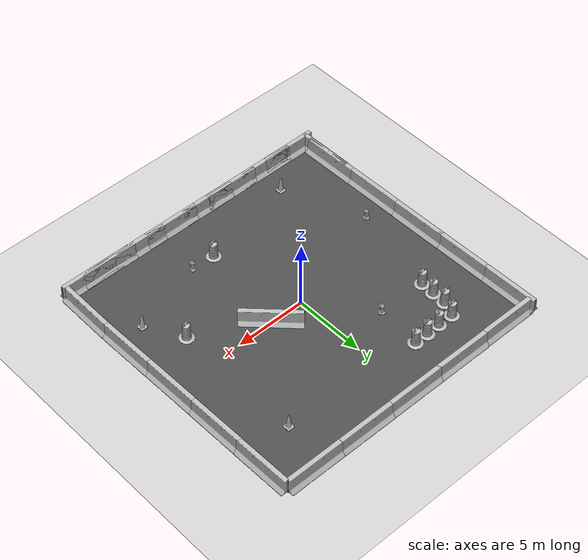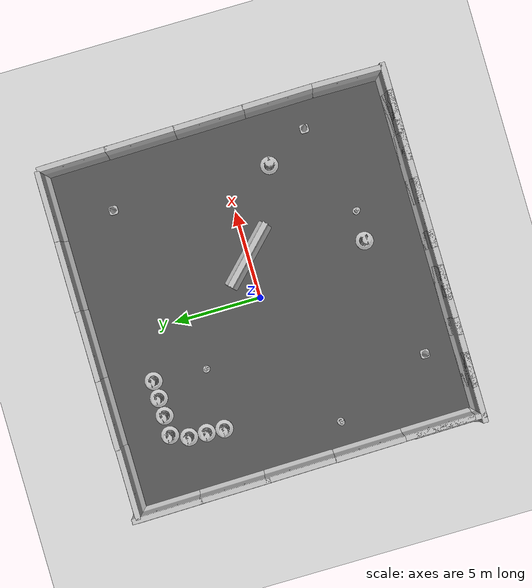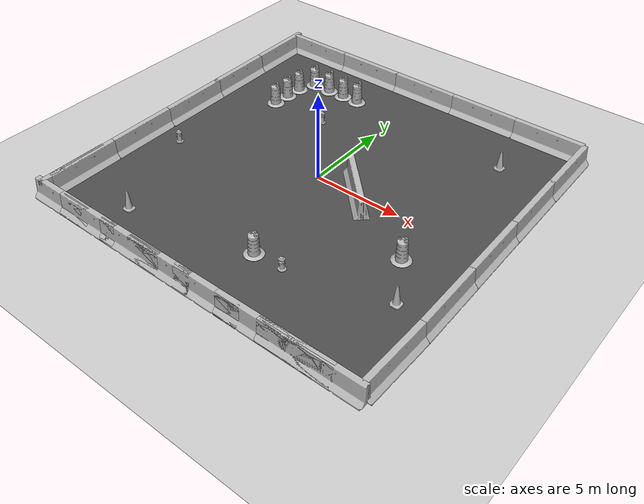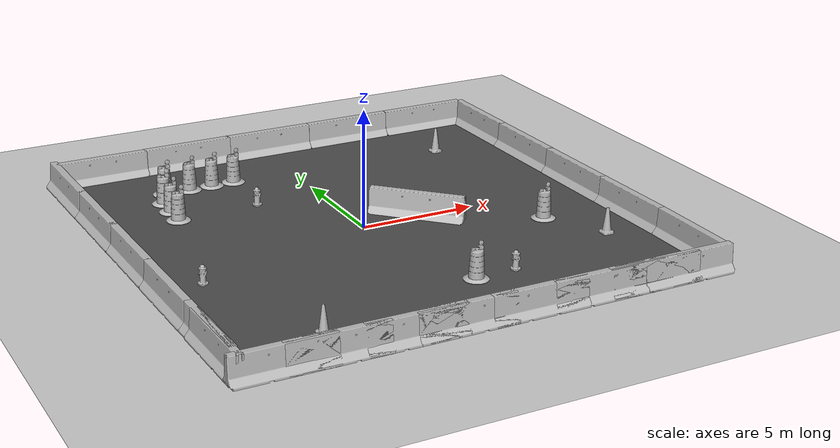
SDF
<sdf version="1.6">
 <world name="default">
  <light name="sun" type="directional">
   <pose>0 0 10 0 -0 0</pose>
   <diffuse>0.8 0.8 0.8 1</diffuse>
   <specular>0.2 0.2 0.2 1</specular>
   <attenuation>
    <range>1000</range>
    <constant>0.9</constant>
    <linear>0.01</linear>
    <quadratic>0.001</quadratic>
   </attenuation>
   <direction>-0.5 0.1 -0.9</direction>
  </light>
  <model name="ground_plane">
   <static>1</static>
   <link name="link">
    <collision name="collision">
     <geometry><plane><normal>0 0 1</normal><size>100 100</size></plane></geometry>
     <surface><friction><ode><mu>100</mu><mu2>50</mu2></ode></friction></surface>
    </collision>
    <visual name="visual">
     <cast_shadows>0</cast_shadows>
     <geometry><plane><normal>0 0 1</normal><size>100 100</size></plane></geometry>
     <material>
      <script><uri>file://media/materials/scripts/gazebo.material</uri><name>Gazebo/Grey</name></script>
     </material>
    </visual>
    <velocity_decay><linear>0</linear><angular>0</angular></velocity_decay>
   </link>
  </model>
  <physics name="default_physics" default="0" type="ode">
   <max_step_size>0.01</max_step_size>
   <real_time_factor>1</real_time_factor>
   <real_time_update_rate>100</real_time_update_rate>
  </physics>
  <scene><ambient>0.4 0.4 0.4 1</ambient><background>0.7 0.7 0.7 1</background><shadows>1</shadows></scene>
  <model name="jersey_barrier">
   <static>1</static>
   <link name="link">
    <visual name="visual">
     <geometry><mesh><uri>model://jersey_barrier/meshes/jersey_barrier.dae</uri></mesh></geometry>
    </visual>
    <collision name="upright">
     <pose>0 0 0.5715 0 -0 0</pose>
     <geometry><box><size>4.06542 0.3063 1.143</size></box></geometry>
    </collision>
    <collision name="base">
     <pose>0 0 0.032258 0 -0 0</pose>
     <geometry><box><size>4.06542 0.8107 0.064516</size></box></geometry>
    </collision>
    <collision name="base2">
     <pose>0 0 0.1 0 -0 0</pose>
     <geometry><box><size>4.06542 0.65 0.1</size></box></geometry>
    </collision>
    <collision name="base3">
     <pose>0 0 0.2 0 -0 0</pose>
     <geometry><box><size>4.06542 0.5 0.1</size></box></geometry>
    </collision>
    <collision name="left-angle">
     <pose>0 -0.224 0.2401 0.9 -0 0</pose>
     <geometry><box><size>4.06542 0.5 0.064516</size></box></geometry>
    </collision>
    <collision name="right-angle">
     <pose>0 0.224 0.2401 -0.9 0 0</pose>
     <geometry><box><size>4.06542 0.5 0.064516</size></box></geometry>
    </collision>
    <velocity_decay><linear>0</linear><angular>0</angular></velocity_decay>
   </link>
   <pose>-8 -10 0 0 -0 0</pose>
  </model>
  <model name="jersey_barrier_0">
   <static>1</static>
   <link name="link">
    <visual name="visual">
     <geometry><mesh><uri>model://jersey_barrier/meshes/jersey_barrier.dae</uri></mesh></geometry>
    </visual>
    <collision name="upright">
     <pose>0 0 0.5715 0 -0 0</pose>
     <geometry><box><size>4.06542 0.3063 1.143</size></box></geometry>
    </collision>
    <collision name="base">
     <pose>0 0 0.032258 0 -0 0</pose>
     <geometry><box><size>4.06542 0.8107 0.064516</size></box></geometry>
    </collision>
    <collision name="base2">
     <pose>0 0 0.1 0 -0 0</pose>
     <geometry><box><size>4.06542 0.65 0.1</size></box></geometry>
    </collision>
    <collision name="base3">
     <pose>0 0 0.2 0 -0 0</pose>
     <geometry><box><size>4.06542 0.5 0.1</size></box></geometry>
    </collision>
    <collision name="left-angle">
     <pose>0 -0.224 0.2401 0.9 -0 0</pose>
     <geometry><box><size>4.06542 0.5 0.064516</size></box></geometry>
    </collision>
    <collision name="right-angle">
     <pose>0 0.224 0.2401 -0.9 0 0</pose>
     <geometry><box><size>4.06542 0.5 0.064516</size></box></geometry>
    </collision>
    <velocity_decay><linear>0</linear><angular>0</angular></velocity_decay>
   </link>
   <pose>-3 -10 0 0 -0 0</pose>
  </model>
  <model name="jersey_barrier_1">
   <static>1</static>
   <link name="link">
    <visual name="visual">
     <geometry><mesh><uri>model://jersey_barrier/meshes/jersey_barrier.dae</uri></mesh></geometry>
    </visual>
    <collision name="upright">
     <pose>0 0 0.5715 0 -0 0</pose>
     <geometry><box><size>4.06542 0.3063 1.143</size></box></geometry>
    </collision>
    <collision name="base">
     <pose>0 0 0.032258 0 -0 0</pose>
     <geometry><box><size>4.06542 0.8107 0.064516</size></box></geometry>
    </collision>
    <collision name="base2">
     <pose>0 0 0.1 0 -0 0</pose>
     <geometry><box><size>4.06542 0.65 0.1</size></box></geometry>
    </collision>
    <collision name="base3">
     <pose>0 0 0.2 0 -0 0</pose>
     <geometry><box><size>4.06542 0.5 0.1</size></box></geometry>
    </collision>
    <collision name="left-angle">
     <pose>0 -0.224 0.2401 0.9 -0 0</pose>
     <geometry><box><size>4.06542 0.5 0.064516</size></box></geometry>
    </collision>
    <collision name="right-angle">
     <pose>0 0.224 0.2401 -0.9 0 0</pose>
     <geometry><box><size>4.06542 0.5 0.064516</size></box></geometry>
    </collision>
    <velocity_decay><linear>0</linear><angular>0</angular></velocity_decay>
   </link>
   <pose>2 -10 0 0 -0 0</pose>
  </model>
  <model name="jersey_barrier_2">
   <static>1</static>
   <link name="link">
    <visual name="visual">
     <geometry><mesh><uri>model://jersey_barrier/meshes/jersey_barrier.dae</uri></mesh></geometry>
    </visual>
    <collision name="upright">
     <pose>0 0 0.5715 0 -0 0</pose>
     <geometry><box><size>4.06542 0.3063 1.143</size></box></geometry>
    </collision>
    <collision name="base">
     <pose>0 0 0.032258 0 -0 0</pose>
     <geometry><box><size>4.06542 0.8107 0.064516</size></box></geometry>
    </collision>
    <collision name="base2">
     <pose>0 0 0.1 0 -0 0</pose>
     <geometry><box><size>4.06542 0.65 0.1</size></box></geometry>
    </collision>
    <collision name="base3">
     <pose>0 0 0.2 0 -0 0</pose>
     <geometry><box><size>4.06542 0.5 0.1</size></box></geometry>
    </collision>
    <collision name="left-angle">
     <pose>0 -0.224 0.2401 0.9 -0 0</pose>
     <geometry><box><size>4.06542 0.5 0.064516</size></box></geometry>
    </collision>
    <collision name="right-angle">
     <pose>0 0.224 0.2401 -0.9 0 0</pose>
     <geometry><box><size>4.06542 0.5 0.064516</size></box></geometry>
    </collision>
    <velocity_decay><linear>0</linear><angular>0</angular></velocity_decay>
   </link>
   <pose>7 -10 0 0 -0 0</pose>
  </model>
  <model name="fire_hydrant">
   <static>1</static>
   <link name="link">
    <collision name="collision">
     <geometry><mesh><uri>model://fire_hydrant/meshes/fire_hydrant.dae</uri></mesh></geometry>
    </collision>
    <visual name="visual">
     <geometry><mesh><uri>model://fire_hydrant/meshes/fire_hydrant.dae</uri></mesh></geometry>
    </visual>
    <velocity_decay><linear>0</linear><angular>0</angular></velocity_decay>
   </link>
   <pose>3.18024 -6.51118 0 0 -0 0</pose>
  </model>
  <model name="fire_hydrant_0">
   <static>1</static>
   <link name="link">
    <collision name="collision">
     <geometry><mesh><uri>model://fire_hydrant/meshes/fire_hydrant.dae</uri></mesh></geometry>
    </collision>
    <visual name="visual">
     <geometry><mesh><uri>model://fire_hydrant/meshes/fire_hydrant.dae</uri></mesh></geometry>
    </visual>
    <velocity_decay><linear>0</linear><angular>0</angular></velocity_decay>
   </link>
   <pose>-3 4 0 0 -0 0</pose>
  </model>
  <model name="fire_hydrant_1">
   <static>1</static>
   <link name="link">
    <collision name="collision">
     <geometry><mesh><uri>model://fire_hydrant/meshes/fire_hydrant.dae</uri></mesh></geometry>
    </collision>
    <visual name="visual">
     <geometry><mesh><uri>model://fire_hydrant/meshes/fire_hydrant.dae</uri></mesh></geometry>
    </visual>
    <velocity_decay><linear>0</linear><angular>0</angular></velocity_decay>
   </link>
   <pose>-7.90686 -2.41363 0 0 -0 0</pose>
  </model>
  <model name="jersey_barrier_15">
   <static>1</static>
   <link name="link">
    <visual name="visual">
     <geometry><mesh><uri>model://jersey_barrier/meshes/jersey_barrier.dae</uri></mesh></geometry>
    </visual>
    <collision name="upright">
     <pose>0 0 0.5715 0 -0 0</pose>
     <geometry><box><size>4.06542 0.3063 1.143</size></box></geometry>
    </collision>
    <collision name="base">
     <pose>0 0 0.032258 0 -0 0</pose>
     <geometry><box><size>4.06542 0.8107 0.064516</size></box></geometry>
    </collision>
    <collision name="base2">
     <pose>0 0 0.1 0 -0 0</pose>
     <geometry><box><size>4.06542 0.65 0.1</size></box></geometry>
    </collision>
    <collision name="base3">
     <pose>0 0 0.2 0 -0 0</pose>
     <geometry><box><size>4.06542 0.5 0.1</size></box></geometry>
    </collision>
    <collision name="left-angle">
     <pose>0 -0.224 0.2401 0.9 -0 0</pose>
     <geometry><box><size>4.06542 0.5 0.064516</size></box></geometry>
    </collision>
    <collision name="right-angle">
     <pose>0 0.224 0.2401 -0.9 0 0</pose>
     <geometry><box><size>4.06542 0.5 0.064516</size></box></geometry>
    </collision>
    <velocity_decay><linear>0</linear><angular>0</angular></velocity_decay>
   </link>
   <pose>2.45495 0 0 0 -0 2.36</pose>
  </model>
  <model name="Construction Cone">
   <link name="link">
    <collision name="collision">
     <geometry>
      <mesh><scale>10 10 10</scale><uri>model://construction_cone/meshes/construction_cone.dae</uri></mesh>
     </geometry>
    </collision>
    <visual name="visual">
     <geometry>
      <mesh><scale>10 10 10</scale><uri>model://construction_cone/meshes/construction_cone.dae</uri></mesh>
     </geometry>
    </visual>
    <velocity_decay><linear>0</linear><angular>0</angular></velocity_decay>
    <inertial>
     <inertia><ixx>1</ixx><ixy>0</ixy><ixz>0</ixz><iyy>1</iyy><iyz>0</iyz><izz>1</izz></inertia>
     <mass>1</mass>
    </inertial>
   </link>
   <pose>-5.59121 -8 0.05 -0 -1e-06 2e-06</pose>
   <static>0</static>
  </model>
  <model name="Construction Barrel">
   <link name="link">
    <inertial>
     <pose>0 0 0.4 0 -0 0</pose>
     <mass>500</mass>
     <inertia><ixx>51.2096</ixx><iyy>51.2096</iyy><izz>25</izz><ixy>0</ixy><ixz>0</ixz><iyz>0</iyz></inertia>
    </inertial>
    <collision name="collision">
     <geometry><mesh><uri>model://construction_barrel/meshes/construction_barrel.dae</uri></mesh></geometry>
    </collision>
    <visual name="visual">
     <geometry><mesh><uri>model://construction_barrel/meshes/construction_barrel.dae</uri></mesh></geometry>
    </visual>
    <velocity_decay><linear>0</linear><angular>0</angular></velocity_decay>
   </link>
   <pose>7.00008 -2.54628 0.049877 0.000487 -3e-06 0.000309</pose>
   <static>0</static>
  </model>
  <model name="Construction Cone_0">
   <link name="link">
    <collision name="collision">
     <geometry>
      <mesh><scale>10 10 10</scale><uri>model://construction_cone/meshes/construction_cone.dae</uri></mesh>
     </geometry>
    </collision>
    <visual name="visual">
     <geometry>
      <mesh><scale>10 10 10</scale><uri>model://construction_cone/meshes/construction_cone.dae</uri></mesh>
     </geometry>
    </visual>
    <velocity_decay><linear>0</linear><angular>0</angular></velocity_decay>
    <inertial>
     <inertia><ixx>1</ixx><ixy>0</ixy><ixz>0</ixz><iyy>1</iyy><iyz>0</iyz><izz>1</izz></inertia>
     <mass>1</mass>
    </inertial>
   </link>
   <pose>6.99685 6.55732 0.05 0 -1e-06 -0.00701</pose>
   <static>0</static>
  </model>
  <model name="Construction Barrel_0">
   <link name="link">
    <inertial>
     <pose>0 0 0.4 0 -0 0</pose>
     <mass>500</mass>
     <inertia><ixx>51.2096</ixx><iyy>51.2096</iyy><izz>25</izz><ixy>0</ixy><ixz>0</ixz><iyz>0</iyz></inertia>
    </inertial>
    <collision name="collision">
     <geometry><mesh><uri>model://construction_barrel/meshes/construction_barrel.dae</uri></mesh></geometry>
    </collision>
    <visual name="visual">
     <geometry><mesh><uri>model://construction_barrel/meshes/construction_barrel.dae</uri></mesh></geometry>
    </visual>
    <velocity_decay><linear>0</linear><angular>0</angular></velocity_decay>
   </link>
   <pose>1.4518 -6.51121 0.049917 -0.000164 -0.000339 -5.5e-05</pose>
   <static>0</static>
  </model>
  <model name="asphalt_plane">
   <static>1</static>
   <link name="link">
    <collision name="collision"><geometry><box><size>20 20 0.1</size></box></geometry></collision>
    <visual name="visual">
     <cast_shadows>0</cast_shadows>
     <geometry><box><size>20 20 0.1</size></box></geometry>
     <material>
      <script>
       <uri>model://asphalt_plane/materials/scripts</uri>
       <uri>model://asphalt_plane/materials/textures</uri>
       <name>vrc/asphalt</name>
      </script>
     </material>
    </visual>
    <velocity_decay><linear>0</linear><angular>0</angular></velocity_decay>
   </link>
   <pose>0.076733 -0.110379 0 0 -0 0</pose>
  </model>
  <model name="Construction Barrel_1">
   <link name="link">
    <inertial>
     <pose>0 0 0.4 0 -0 0</pose>
     <mass>500</mass>
     <inertia><ixx>51.2096</ixx><iyy>51.2096</iyy><izz>25</izz><ixy>0</ixy><ixz>0</ixz><iyz>0</iyz></inertia>
    </inertial>
    <collision name="collision">
     <geometry><mesh><uri>model://construction_barrel/meshes/construction_barrel.dae</uri></mesh></geometry>
    </collision>
    <visual name="visual">
     <geometry><mesh><uri>model://construction_barrel/meshes/construction_barrel.dae</uri></mesh></geometry>
    </visual>
    <velocity_decay><linear>0</linear><angular>0</angular></velocity_decay>
   </link>
   <pose>-6.50467 3.98277 0.049886 0.000435 0.000115 -0.009564</pose>
   <static>0</static>
  </model>
  <model name="Construction Barrel_2">
   <link name="link">
    <inertial>
     <pose>0 0 0.4 0 -0 0</pose>
     <mass>500</mass>
     <inertia><ixx>51.2096</ixx><iyy>51.2096</iyy><izz>25</izz><ixy>0</ixy><ixz>0</ixz><iyz>0</iyz></inertia>
    </inertial>
    <collision name="collision">
     <geometry><mesh><uri>model://construction_barrel/meshes/construction_barrel.dae</uri></mesh></geometry>
    </collision>
    <visual name="visual">
     <geometry><mesh><uri>model://construction_barrel/meshes/construction_barrel.dae</uri></mesh></geometry>
    </visual>
    <velocity_decay><linear>0</linear><angular>0</angular></velocity_decay>
   </link>
   <pose>-6.45061 4.99646 0.04991 -0.000176 -0.000354 0.064909</pose>
   <static>0</static>
  </model>
  <model name="Construction Barrel_3">
   <link name="link">
    <inertial>
     <pose>0 0 0.4 0 -0 0</pose>
     <mass>500</mass>
     <inertia><ixx>51.2096</ixx><iyy>51.2096</iyy><izz>25</izz><ixy>0</ixy><ixz>0</ixz><iyz>0</iyz></inertia>
    </inertial>
    <collision name="collision">
     <geometry><mesh><uri>model://construction_barrel/meshes/construction_barrel.dae</uri></mesh></geometry>
    </collision>
    <visual name="visual">
     <geometry><mesh><uri>model://construction_barrel/meshes/construction_barrel.dae</uri></mesh></geometry>
    </visual>
    <velocity_decay><linear>0</linear><angular>0</angular></velocity_decay>
   </link>
   <pose>-6.4017 6.01119 0.049863 -0.000145 -0.0005 -0.120744</pose>
   <static>0</static>
  </model>
  <model name="Construction Barrel_4">
   <link name="link">
    <inertial>
     <pose>0 0 0.4 0 -0 0</pose>
     <mass>500</mass>
     <inertia><ixx>51.2096</ixx><iyy>51.2096</iyy><izz>25</izz><ixy>0</ixy><ixz>0</ixz><iyz>0</iyz></inertia>
    </inertial>
    <collision name="collision">
     <geometry><mesh><uri>model://construction_barrel/meshes/construction_barrel.dae</uri></mesh></geometry>
    </collision>
    <visual name="visual">
     <geometry><mesh><uri>model://construction_barrel/meshes/construction_barrel.dae</uri></mesh></geometry>
    </visual>
    <velocity_decay><linear>0</linear><angular>0</angular></velocity_decay>
   </link>
   <pose>-6.0062 7.00897 0.0499 0.000407 9.3e-05 -0.049538</pose>
   <static>0</static>
  </model>
  <model name="Construction Barrel_5">
   <link name="link">
    <inertial>
     <pose>0 0 0.4 0 -0 0</pose>
     <mass>500</mass>
     <inertia><ixx>51.2096</ixx><iyy>51.2096</iyy><izz>25</izz><ixy>0</ixy><ixz>0</ixz><iyz>0</iyz></inertia>
    </inertial>
    <collision name="collision">
     <geometry><mesh><uri>model://construction_barrel/meshes/construction_barrel.dae</uri></mesh></geometry>
    </collision>
    <visual name="visual">
     <geometry><mesh><uri>model://construction_barrel/meshes/construction_barrel.dae</uri></mesh></geometry>
    </visual>
    <velocity_decay><linear>0</linear><angular>0</angular></velocity_decay>
   </link>
   <pose>-4.8756 7.0082 0.049921 -0.000156 -0.000328 0.146114</pose>
   <static>0</static>
  </model>
  <model name="Construction Barrel_6">
   <link name="link">
    <inertial>
     <pose>0 0 0.4 0 -0 0</pose>
     <mass>500</mass>
     <inertia><ixx>51.2096</ixx><iyy>51.2096</iyy><izz>25</izz><ixy>0</ixy><ixz>0</ixz><iyz>0</iyz></inertia>
    </inertial>
    <collision name="collision">
     <geometry><mesh><uri>model://construction_barrel/meshes/construction_barrel.dae</uri></mesh></geometry>
    </collision>
    <visual name="visual">
     <geometry><mesh><uri>model://construction_barrel/meshes/construction_barrel.dae</uri></mesh></geometry>
    </visual>
    <velocity_decay><linear>0</linear><angular>0</angular></velocity_decay>
   </link>
   <pose>-3.84411 7.04008 0.049888 1e-06 -0.000441 0.022475</pose>
   <static>0</static>
  </model>
  <model name="Construction Barrel_7">
   <link name="link">
    <inertial>
     <pose>0 0 0.4 0 -0 0</pose>
     <mass>500</mass>
     <inertia><ixx>51.2096</ixx><iyy>51.2096</iyy><izz>25</izz><ixy>0</ixy><ixz>0</ixz><iyz>0</iyz></inertia>
    </inertial>
    <collision name="collision">
     <geometry><mesh><uri>model://construction_barrel/meshes/construction_barrel.dae</uri></mesh></geometry>
    </collision>
    <visual name="visual">
     <geometry><mesh><uri>model://construction_barrel/meshes/construction_barrel.dae</uri></mesh></geometry>
    </visual>
    <velocity_decay><linear>0</linear><angular>0</angular></velocity_decay>
   </link>
   <pose>-2.82746 7.06011 0.049884 -0.000115 -0.000453 0.075127</pose>
   <static>0</static>
  </model>
  <model name="Construction Cone_1">
   <link name="link">
    <collision name="collision">
     <geometry>
      <mesh><scale>10 10 10</scale><uri>model://construction_cone/meshes/construction_cone.dae</uri></mesh>
     </geometry>
    </collision>
    <visual name="visual">
     <geometry>
      <mesh><scale>10 10 10</scale><uri>model://construction_cone/meshes/construction_cone.dae</uri></mesh>
     </geometry>
    </visual>
    <velocity_decay><linear>0</linear><angular>0</angular></velocity_decay>
    <inertial>
     <inertia><ixx>1</ixx><ixy>0</ixy><ixz>0</ixz><iyy>1</iyy><iyz>0</iyz><izz>1</izz></inertia>
     <mass>1</mass>
    </inertial>
   </link>
   <pose>8.42887 -5 0.04902 1e-06 -0 2e-06</pose>
   <static>0</static>
  </model>
  <gravity>0 0 -9.8</gravity>
  <magnetic_field>6e-06 2.3e-05 -4.2e-05</magnetic_field>
  <atmosphere type="adiabatic"/>
  <spherical_coordinates>
   <surface_model>EARTH_WGS84</surface_model>
   <latitude_deg>0</latitude_deg>
   <longitude_deg>0</longitude_deg>
   <elevation>0</elevation>
   <heading_deg>0</heading_deg>
  </spherical_coordinates>
  <model name="jersey_barrier_16">
   <static>1</static>
   <link name="link">
    <visual name="visual">
     <geometry><mesh><uri>model://jersey_barrier/meshes/jersey_barrier.dae</uri></mesh></geometry>
    </visual>
    <collision name="upright">
     <pose>0 0 0.5715 0 -0 0</pose>
     <geometry><box><size>4.06542 0.3063 1.143</size></box></geometry>
    </collision>
    <collision name="base">
     <pose>0 0 0.032258 0 -0 0</pose>
     <geometry><box><size>4.06542 0.8107 0.064516</size></box></geometry>
    </collision>
    <collision name="base2">
     <pose>0 0 0.1 0 -0 0</pose>
     <geometry><box><size>4.06542 0.65 0.1</size></box></geometry>
    </collision>
    <collision name="base3">
     <pose>0 0 0.2 0 -0 0</pose>
     <geometry><box><size>4.06542 0.5 0.1</size></box></geometry>
    </collision>
    <collision name="left-angle">
     <pose>0 -0.224 0.2401 0.9 -0 0</pose>
     <geometry><box><size>4.06542 0.5 0.064516</size></box></geometry>
    </collision>
    <collision name="right-angle">
     <pose>0 0.224 0.2401 -0.9 0 0</pose>
     <geometry><box><size>4.06542 0.5 0.064516</size></box></geometry>
    </collision>
   </link>
   <pose>4.59491 -10 0 0 -0 0</pose>
  </model>
  <model name="jersey_barrier_17">
   <static>1</static>
   <link name="link">
    <visual name="visual">
     <geometry><mesh><uri>model://jersey_barrier/meshes/jersey_barrier.dae</uri></mesh></geometry>
    </visual>
    <collision name="upright">
     <pose>0 0 0.5715 0 -0 0</pose>
     <geometry><box><size>4.06542 0.3063 1.143</size></box></geometry>
    </collision>
    <collision name="base">
     <pose>0 0 0.032258 0 -0 0</pose>
     <geometry><box><size>4.06542 0.8107 0.064516</size></box></geometry>
    </collision>
    <collision name="base2">
     <pose>0 0 0.1 0 -0 0</pose>
     <geometry><box><size>4.06542 0.65 0.1</size></box></geometry>
    </collision>
    <collision name="base3">
     <pose>0 0 0.2 0 -0 0</pose>
     <geometry><box><size>4.06542 0.5 0.1</size></box></geometry>
    </collision>
    <collision name="left-angle">
     <pose>0 -0.224 0.2401 0.9 -0 0</pose>
     <geometry><box><size>4.06542 0.5 0.064516</size></box></geometry>
    </collision>
    <collision name="right-angle">
     <pose>0 0.224 0.2401 -0.9 0 0</pose>
     <geometry><box><size>4.06542 0.5 0.064516</size></box></geometry>
    </collision>
   </link>
   <pose>-1 -10 0 0 -0 0</pose>
  </model>
  <model name="jersey_barrier_18">
   <static>1</static>
   <link name="link">
    <visual name="visual">
     <geometry><mesh><uri>model://jersey_barrier/meshes/jersey_barrier.dae</uri></mesh></geometry>
    </visual>
    <collision name="upright">
     <pose>0 0 0.5715 0 -0 0</pose>
     <geometry><box><size>4.06542 0.3063 1.143</size></box></geometry>
    </collision>
    <collision name="base">
     <pose>0 0 0.032258 0 -0 0</pose>
     <geometry><box><size>4.06542 0.8107 0.064516</size></box></geometry>
    </collision>
    <collision name="base2">
     <pose>0 0 0.1 0 -0 0</pose>
     <geometry><box><size>4.06542 0.65 0.1</size></box></geometry>
    </collision>
    <collision name="base3">
     <pose>0 0 0.2 0 -0 0</pose>
     <geometry><box><size>4.06542 0.5 0.1</size></box></geometry>
    </collision>
    <collision name="left-angle">
     <pose>0 -0.224 0.2401 0.9 -0 0</pose>
     <geometry><box><size>4.06542 0.5 0.064516</size></box></geometry>
    </collision>
    <collision name="right-angle">
     <pose>0 0.224 0.2401 -0.9 0 0</pose>
     <geometry><box><size>4.06542 0.5 0.064516</size></box></geometry>
    </collision>
   </link>
   <pose>-6 -10 0 0 -0 0</pose>
  </model>
  <model name="jersey_barrier_19">
   <static>1</static>
   <link name="link">
    <visual name="visual">
     <geometry><mesh><uri>model://jersey_barrier/meshes/jersey_barrier.dae</uri></mesh></geometry>
    </visual>
    <collision name="upright">
     <pose>0 0 0.5715 0 -0 0</pose>
     <geometry><box><size>4.06542 0.3063 1.143</size></box></geometry>
    </collision>
    <collision name="base">
     <pose>0 0 0.032258 0 -0 0</pose>
     <geometry><box><size>4.06542 0.8107 0.064516</size></box></geometry>
    </collision>
    <collision name="base2">
     <pose>0 0 0.1 0 -0 0</pose>
     <geometry><box><size>4.06542 0.65 0.1</size></box></geometry>
    </collision>
    <collision name="base3">
     <pose>0 0 0.2 0 -0 0</pose>
     <geometry><box><size>4.06542 0.5 0.1</size></box></geometry>
    </collision>
    <collision name="left-angle">
     <pose>0 -0.224 0.2401 0.9 -0 0</pose>
     <geometry><box><size>4.06542 0.5 0.064516</size></box></geometry>
    </collision>
    <collision name="right-angle">
     <pose>0 0.224 0.2401 -0.9 0 0</pose>
     <geometry><box><size>4.06542 0.5 0.064516</size></box></geometry>
    </collision>
   </link>
   <pose>8.53416 -10 0 0 -0 0</pose>
  </model>
  <model name="jersey_barrier_12">
   <link name="link">
    <pose>-0.324032 -0.254007 0 0 -0 0</pose>
    <velocity_decay><linear>0</linear><angular>0</angular></velocity_decay>
    <visual name="visual">
     <geometry><mesh><uri>model://jersey_barrier/meshes/jersey_barrier.dae</uri></mesh></geometry>
     <material><shader type="pixel"/></material>
    </visual>
    <collision name="upright">
     <pose>0 0 0.5715 0 -0 0</pose>
     <geometry><box><size>4.06542 0.3063 1.143</size></box></geometry>
     <surface>
      <friction>
       <ode><mu>1</mu><mu2>1</mu2><fdir1>0 0 0</fdir1><slip1>0</slip1><slip2>0</slip2></ode>
       <torsional>
        <coefficient>1</coefficient>
        <patch_radius>0</patch_radius>
        <surface_radius>0</surface_radius>
        <use_patch_radius>1</use_patch_radius>
        <ode><slip>0</slip></ode>
       </torsional>
      </friction>
      <bounce><restitution_coefficient>0</restitution_coefficient><threshold>1e+06</threshold></bounce>
      <contact>
       <collide_without_contact>0</collide_without_contact>
       <collide_without_contact_bitmask>1</collide_without_contact_bitmask>
       <collide_bitmask>1</collide_bitmask>
       <ode>
        <soft_cfm>0</soft_cfm>
        <soft_erp>0.2</soft_erp>
        <kp>1e+13</kp>
        <kd>1</kd>
        <max_vel>0.01</max_vel>
        <min_depth>0</min_depth>
       </ode>
       <bullet>
        <split_impulse>1</split_impulse>
        <split_impulse_penetration_threshold>-0.01</split_impulse_penetration_threshold>
        <soft_cfm>0</soft_cfm>
        <soft_erp>0.2</soft_erp>
        <kp>1e+13</kp>
        <kd>1</kd>
       </bullet>
      </contact>
     </surface>
    </collision>
    <collision name="base">
     <pose>0 0 0.032258 0 -0 0</pose>
     <geometry><box><size>4.06542 0.8107 0.064516</size></box></geometry>
     <surface>
      <friction>
       <ode><mu>1</mu><mu2>1</mu2><fdir1>0 0 0</fdir1><slip1>0</slip1><slip2>0</slip2></ode>
       <torsional>
        <coefficient>1</coefficient>
        <patch_radius>0</patch_radius>
        <surface_radius>0</surface_radius>
        <use_patch_radius>1</use_patch_radius>
        <ode><slip>0</slip></ode>
       </torsional>
      </friction>
      <bounce><restitution_coefficient>0</restitution_coefficient><threshold>1e+06</threshold></bounce>
      <contact>
       <collide_without_contact>0</collide_without_contact>
       <collide_without_contact_bitmask>1</collide_without_contact_bitmask>
       <collide_bitmask>1</collide_bitmask>
       <ode>
        <soft_cfm>0</soft_cfm>
        <soft_erp>0.2</soft_erp>
        <kp>1e+13</kp>
        <kd>1</kd>
        <max_vel>0.01</max_vel>
        <min_depth>0</min_depth>
       </ode>
       <bullet>
        <split_impulse>1</split_impulse>
        <split_impulse_penetration_threshold>-0.01</split_impulse_penetration_threshold>
        <soft_cfm>0</soft_cfm>
        <soft_erp>0.2</soft_erp>
        <kp>1e+13</kp>
        <kd>1</kd>
       </bullet>
      </contact>
     </surface>
    </collision>
    <collision name="base3">
     <pose>0 0 0.2 0 -0 0</pose>
     <geometry><box><size>4.06542 0.5 0.1</size></box></geometry>
     <surface>
      <friction>
       <ode><mu>1</mu><mu2>1</mu2><fdir1>0 0 0</fdir1><slip1>0</slip1><slip2>0</slip2></ode>
       <torsional>
        <coefficient>1</coefficient>
        <patch_radius>0</patch_radius>
        <surface_radius>0</surface_radius>
        <use_patch_radius>1</use_patch_radius>
        <ode><slip>0</slip></ode>
       </torsional>
      </friction>
      <bounce><restitution_coefficient>0</restitution_coefficient><threshold>1e+06</threshold></bounce>
      <contact>
       <collide_without_contact>0</collide_without_contact>
       <collide_without_contact_bitmask>1</collide_without_contact_bitmask>
       <collide_bitmask>1</collide_bitmask>
       <ode>
        <soft_cfm>0</soft_cfm>
        <soft_erp>0.2</soft_erp>
        <kp>1e+13</kp>
        <kd>1</kd>
        <max_vel>0.01</max_vel>
        <min_depth>0</min_depth>
       </ode>
       <bullet>
        <split_impulse>1</split_impulse>
        <split_impulse_penetration_threshold>-0.01</split_impulse_penetration_threshold>
        <soft_cfm>0</soft_cfm>
        <soft_erp>0.2</soft_erp>
        <kp>1e+13</kp>
        <kd>1</kd>
       </bullet>
      </contact>
     </surface>
    </collision>
    <collision name="base2">
     <pose>0 0 0.1 0 -0 0</pose>
     <geometry><box><size>4.06542 0.65 0.1</size></box></geometry>
     <surface>
      <friction>
       <ode><mu>1</mu><mu2>1</mu2><fdir1>0 0 0</fdir1><slip1>0</slip1><slip2>0</slip2></ode>
       <torsional>
        <coefficient>1</coefficient>
        <patch_radius>0</patch_radius>
        <surface_radius>0</surface_radius>
        <use_patch_radius>1</use_patch_radius>
        <ode><slip>0</slip></ode>
       </torsional>
      </friction>
      <bounce><restitution_coefficient>0</restitution_coefficient><threshold>1e+06</threshold></bounce>
      <contact>
       <collide_without_contact>0</collide_without_contact>
       <collide_without_contact_bitmask>1</collide_without_contact_bitmask>
       <collide_bitmask>1</collide_bitmask>
       <ode>
        <soft_cfm>0</soft_cfm>
        <soft_erp>0.2</soft_erp>
        <kp>1e+13</kp>
        <kd>1</kd>
        <max_vel>0.01</max_vel>
        <min_depth>0</min_depth>
       </ode>
       <bullet>
        <split_impulse>1</split_impulse>
        <split_impulse_penetration_threshold>-0.01</split_impulse_penetration_threshold>
        <soft_cfm>0</soft_cfm>
        <soft_erp>0.2</soft_erp>
        <kp>1e+13</kp>
        <kd>1</kd>
       </bullet>
      </contact>
     </surface>
    </collision>
    <collision name="left-angle">
     <pose>0 -0.224 0.2401 0.9 -0 0</pose>
     <geometry><box><size>4.06542 0.5 0.064516</size></box></geometry>
     <surface>
      <friction>
       <ode><mu>1</mu><mu2>1</mu2><fdir1>0 0 0</fdir1><slip1>0</slip1><slip2>0</slip2></ode>
       <torsional>
        <coefficient>1</coefficient>
        <patch_radius>0</patch_radius>
        <surface_radius>0</surface_radius>
        <use_patch_radius>1</use_patch_radius>
        <ode><slip>0</slip></ode>
       </torsional>
      </friction>
      <bounce><restitution_coefficient>0</restitution_coefficient><threshold>1e+06</threshold></bounce>
      <contact>
       <collide_without_contact>0</collide_without_contact>
       <collide_without_contact_bitmask>1</collide_without_contact_bitmask>
       <collide_bitmask>1</collide_bitmask>
       <ode>
        <soft_cfm>0</soft_cfm>
        <soft_erp>0.2</soft_erp>
        <kp>1e+13</kp>
        <kd>1</kd>
        <max_vel>0.01</max_vel>
        <min_depth>0</min_depth>
       </ode>
       <bullet>
        <split_impulse>1</split_impulse>
        <split_impulse_penetration_threshold>-0.01</split_impulse_penetration_threshold>
        <soft_cfm>0</soft_cfm>
        <soft_erp>0.2</soft_erp>
        <kp>1e+13</kp>
        <kd>1</kd>
       </bullet>
      </contact>
     </surface>
    </collision>
    <collision name="right-angle">
     <pose>0 0.224 0.2401 -0.9 0 0</pose>
     <geometry><box><size>4.06542 0.5 0.064516</size></box></geometry>
     <surface>
      <friction>
       <ode><mu>1</mu><mu2>1</mu2><fdir1>0 0 0</fdir1><slip1>0</slip1><slip2>0</slip2></ode>
       <torsional>
        <coefficient>1</coefficient>
        <patch_radius>0</patch_radius>
        <surface_radius>0</surface_radius>
        <use_patch_radius>1</use_patch_radius>
        <ode><slip>0</slip></ode>
       </torsional>
      </friction>
      <bounce><restitution_coefficient>0</restitution_coefficient><threshold>1e+06</threshold></bounce>
      <contact>
       <collide_without_contact>0</collide_without_contact>
       <collide_without_contact_bitmask>1</collide_without_contact_bitmask>
       <collide_bitmask>1</collide_bitmask>
       <ode>
        <soft_cfm>0</soft_cfm>
        <soft_erp>0.2</soft_erp>
        <kp>1e+13</kp>
        <kd>1</kd>
        <max_vel>0.01</max_vel>
        <min_depth>0</min_depth>
       </ode>
       <bullet>
        <split_impulse>1</split_impulse>
        <split_impulse_penetration_threshold>-0.01</split_impulse_penetration_threshold>
        <soft_cfm>0</soft_cfm>
        <soft_erp>0.2</soft_erp>
        <kp>1e+13</kp>
        <kd>1</kd>
       </bullet>
      </contact>
     </surface>
    </collision>
   </link>
   <static>1</static>
   <pose>10.0879 -7.62158 0 0 -0 1.56</pose>
  </model>
  <model name="jersey_barrier_3">
   <static>1</static>
   <link name="link">
    <visual name="visual">
     <geometry><mesh><uri>model://jersey_barrier/meshes/jersey_barrier.dae</uri></mesh></geometry>
    </visual>
    <collision name="upright">
     <pose>0 0 0.5715 0 -0 0</pose>
     <geometry><box><size>4.06542 0.3063 1.143</size></box></geometry>
    </collision>
    <collision name="base">
     <pose>0 0 0.032258 0 -0 0</pose>
     <geometry><box><size>4.06542 0.8107 0.064516</size></box></geometry>
    </collision>
    <collision name="base2">
     <pose>0 0 0.1 0 -0 0</pose>
     <geometry><box><size>4.06542 0.65 0.1</size></box></geometry>
    </collision>
    <collision name="base3">
     <pose>0 0 0.2 0 -0 0</pose>
     <geometry><box><size>4.06542 0.5 0.1</size></box></geometry>
    </collision>
    <collision name="left-angle">
     <pose>0 -0.224 0.2401 0.9 -0 0</pose>
     <geometry><box><size>4.06542 0.5 0.064516</size></box></geometry>
    </collision>
    <collision name="right-angle">
     <pose>0 0.224 0.2401 -0.9 0 0</pose>
     <geometry><box><size>4.06542 0.5 0.064516</size></box></geometry>
    </collision>
   </link>
   <pose>8.05371 9.8555 0 0 -0 0</pose>
  </model>
  <model name="jersey_barrier_4">
   <static>1</static>
   <link name="link">
    <visual name="visual">
     <geometry><mesh><uri>model://jersey_barrier/meshes/jersey_barrier.dae</uri></mesh></geometry>
    </visual>
    <collision name="upright">
     <pose>0 0 0.5715 0 -0 0</pose>
     <geometry><box><size>4.06542 0.3063 1.143</size></box></geometry>
    </collision>
    <collision name="base">
     <pose>0 0 0.032258 0 -0 0</pose>
     <geometry><box><size>4.06542 0.8107 0.064516</size></box></geometry>
    </collision>
    <collision name="base2">
     <pose>0 0 0.1 0 -0 0</pose>
     <geometry><box><size>4.06542 0.65 0.1</size></box></geometry>
    </collision>
    <collision name="base3">
     <pose>0 0 0.2 0 -0 0</pose>
     <geometry><box><size>4.06542 0.5 0.1</size></box></geometry>
    </collision>
    <collision name="left-angle">
     <pose>0 -0.224 0.2401 0.9 -0 0</pose>
     <geometry><box><size>4.06542 0.5 0.064516</size></box></geometry>
    </collision>
    <collision name="right-angle">
     <pose>0 0.224 0.2401 -0.9 0 0</pose>
     <geometry><box><size>4.06542 0.5 0.064516</size></box></geometry>
    </collision>
   </link>
   <pose>4.03403 9.85763 0 0 -0 0</pose>
  </model>
  <model name="jersey_barrier_5">
   <static>1</static>
   <link name="link">
    <visual name="visual">
     <geometry><mesh><uri>model://jersey_barrier/meshes/jersey_barrier.dae</uri></mesh></geometry>
    </visual>
    <collision name="upright">
     <pose>0 0 0.5715 0 -0 0</pose>
     <geometry><box><size>4.06542 0.3063 1.143</size></box></geometry>
    </collision>
    <collision name="base">
     <pose>0 0 0.032258 0 -0 0</pose>
     <geometry><box><size>4.06542 0.8107 0.064516</size></box></geometry>
    </collision>
    <collision name="base2">
     <pose>0 0 0.1 0 -0 0</pose>
     <geometry><box><size>4.06542 0.65 0.1</size></box></geometry>
    </collision>
    <collision name="base3">
     <pose>0 0 0.2 0 -0 0</pose>
     <geometry><box><size>4.06542 0.5 0.1</size></box></geometry>
    </collision>
    <collision name="left-angle">
     <pose>0 -0.224 0.2401 0.9 -0 0</pose>
     <geometry><box><size>4.06542 0.5 0.064516</size></box></geometry>
    </collision>
    <collision name="right-angle">
     <pose>0 0.224 0.2401 -0.9 0 0</pose>
     <geometry><box><size>4.06542 0.5 0.064516</size></box></geometry>
    </collision>
   </link>
   <pose>0.036818 9.84503 0 0 -0 0</pose>
  </model>
  <model name="jersey_barrier_6">
   <static>1</static>
   <link name="link">
    <visual name="visual">
     <geometry><mesh><uri>model://jersey_barrier/meshes/jersey_barrier.dae</uri></mesh></geometry>
    </visual>
    <collision name="upright">
     <pose>0 0 0.5715 0 -0 0</pose>
     <geometry><box><size>4.06542 0.3063 1.143</size></box></geometry>
    </collision>
    <collision name="base">
     <pose>0 0 0.032258 0 -0 0</pose>
     <geometry><box><size>4.06542 0.8107 0.064516</size></box></geometry>
    </collision>
    <collision name="base2">
     <pose>0 0 0.1 0 -0 0</pose>
     <geometry><box><size>4.06542 0.65 0.1</size></box></geometry>
    </collision>
    <collision name="base3">
     <pose>0 0 0.2 0 -0 0</pose>
     <geometry><box><size>4.06542 0.5 0.1</size></box></geometry>
    </collision>
    <collision name="left-angle">
     <pose>0 -0.224 0.2401 0.9 -0 0</pose>
     <geometry><box><size>4.06542 0.5 0.064516</size></box></geometry>
    </collision>
    <collision name="right-angle">
     <pose>0 0.224 0.2401 -0.9 0 0</pose>
     <geometry><box><size>4.06542 0.5 0.064516</size></box></geometry>
    </collision>
   </link>
   <pose>-3.89008 9.84145 0 0 -0 0</pose>
  </model>
  <model name="jersey_barrier_7">
   <static>1</static>
   <link name="link">
    <visual name="visual">
     <geometry><mesh><uri>model://jersey_barrier/meshes/jersey_barrier.dae</uri></mesh></geometry>
    </visual>
    <collision name="upright">
     <pose>0 0 0.5715 0 -0 0</pose>
     <geometry><box><size>4.06542 0.3063 1.143</size></box></geometry>
    </collision>
    <collision name="base">
     <pose>0 0 0.032258 0 -0 0</pose>
     <geometry><box><size>4.06542 0.8107 0.064516</size></box></geometry>
    </collision>
    <collision name="base2">
     <pose>0 0 0.1 0 -0 0</pose>
     <geometry><box><size>4.06542 0.65 0.1</size></box></geometry>
    </collision>
    <collision name="base3">
     <pose>0 0 0.2 0 -0 0</pose>
     <geometry><box><size>4.06542 0.5 0.1</size></box></geometry>
    </collision>
    <collision name="left-angle">
     <pose>0 -0.224 0.2401 0.9 -0 0</pose>
     <geometry><box><size>4.06542 0.5 0.064516</size></box></geometry>
    </collision>
    <collision name="right-angle">
     <pose>0 0.224 0.2401 -0.9 0 0</pose>
     <geometry><box><size>4.06542 0.5 0.064516</size></box></geometry>
    </collision>
   </link>
   <pose>-7.85087 9.81358 0 0 -0 0</pose>
  </model>
  <model name="jersey_barrier_8">
   <link name="link">
    <pose>-0.727355 1.16834 0 0 -0 1.58626</pose>
    <visual name="visual">
     <geometry><mesh><uri>model://jersey_barrier/meshes/jersey_barrier.dae</uri></mesh></geometry>
     <material><shader type="pixel"/></material>
    </visual>
    <collision name="upright">
     <pose>0 0 0.5715 0 -0 0</pose>
     <geometry><box><size>4.06542 0.3063 1.143</size></box></geometry>
     <surface>
      <friction>
       <ode><mu>1</mu><mu2>1</mu2><fdir1>0 0 0</fdir1><slip1>0</slip1><slip2>0</slip2></ode>
       <torsional>
        <coefficient>1</coefficient>
        <patch_radius>0</patch_radius>
        <surface_radius>0</surface_radius>
        <use_patch_radius>1</use_patch_radius>
        <ode><slip>0</slip></ode>
       </torsional>
      </friction>
      <bounce><restitution_coefficient>0</restitution_coefficient><threshold>1e+06</threshold></bounce>
      <contact>
       <collide_without_contact>0</collide_without_contact>
       <collide_without_contact_bitmask>1</collide_without_contact_bitmask>
       <collide_bitmask>1</collide_bitmask>
       <ode>
        <soft_cfm>0</soft_cfm>
        <soft_erp>0.2</soft_erp>
        <kp>1e+13</kp>
        <kd>1</kd>
        <max_vel>0.01</max_vel>
        <min_depth>0</min_depth>
       </ode>
       <bullet>
        <split_impulse>1</split_impulse>
        <split_impulse_penetration_threshold>-0.01</split_impulse_penetration_threshold>
        <soft_cfm>0</soft_cfm>
        <soft_erp>0.2</soft_erp>
        <kp>1e+13</kp>
        <kd>1</kd>
       </bullet>
      </contact>
     </surface>
    </collision>
    <collision name="base">
     <pose>0 0 0.032258 0 -0 0</pose>
     <geometry><box><size>4.06542 0.8107 0.064516</size></box></geometry>
     <surface>
      <friction>
       <ode><mu>1</mu><mu2>1</mu2><fdir1>0 0 0</fdir1><slip1>0</slip1><slip2>0</slip2></ode>
       <torsional>
        <coefficient>1</coefficient>
        <patch_radius>0</patch_radius>
        <surface_radius>0</surface_radius>
        <use_patch_radius>1</use_patch_radius>
        <ode><slip>0</slip></ode>
       </torsional>
      </friction>
      <bounce><restitution_coefficient>0</restitution_coefficient><threshold>1e+06</threshold></bounce>
      <contact>
       <collide_without_contact>0</collide_without_contact>
       <collide_without_contact_bitmask>1</collide_without_contact_bitmask>
       <collide_bitmask>1</collide_bitmask>
       <ode>
        <soft_cfm>0</soft_cfm>
        <soft_erp>0.2</soft_erp>
        <kp>1e+13</kp>
        <kd>1</kd>
        <max_vel>0.01</max_vel>
        <min_depth>0</min_depth>
       </ode>
       <bullet>
        <split_impulse>1</split_impulse>
        <split_impulse_penetration_threshold>-0.01</split_impulse_penetration_threshold>
        <soft_cfm>0</soft_cfm>
        <soft_erp>0.2</soft_erp>
        <kp>1e+13</kp>
        <kd>1</kd>
       </bullet>
      </contact>
     </surface>
    </collision>
    <collision name="base2">
     <pose>0 0 0.1 0 -0 0</pose>
     <geometry><box><size>4.06542 0.65 0.1</size></box></geometry>
     <surface>
      <friction>
       <ode><mu>1</mu><mu2>1</mu2><fdir1>0 0 0</fdir1><slip1>0</slip1><slip2>0</slip2></ode>
       <torsional>
        <coefficient>1</coefficient>
        <patch_radius>0</patch_radius>
        <surface_radius>0</surface_radius>
        <use_patch_radius>1</use_patch_radius>
        <ode><slip>0</slip></ode>
       </torsional>
      </friction>
      <bounce><restitution_coefficient>0</restitution_coefficient><threshold>1e+06</threshold></bounce>
      <contact>
       <collide_without_contact>0</collide_without_contact>
       <collide_without_contact_bitmask>1</collide_without_contact_bitmask>
       <collide_bitmask>1</collide_bitmask>
       <ode>
        <soft_cfm>0</soft_cfm>
        <soft_erp>0.2</soft_erp>
        <kp>1e+13</kp>
        <kd>1</kd>
        <max_vel>0.01</max_vel>
        <min_depth>0</min_depth>
       </ode>
       <bullet>
        <split_impulse>1</split_impulse>
        <split_impulse_penetration_threshold>-0.01</split_impulse_penetration_threshold>
        <soft_cfm>0</soft_cfm>
        <soft_erp>0.2</soft_erp>
        <kp>1e+13</kp>
        <kd>1</kd>
       </bullet>
      </contact>
     </surface>
    </collision>
    <collision name="base3">
     <pose>0 0 0.2 0 -0 0</pose>
     <geometry><box><size>4.06542 0.5 0.1</size></box></geometry>
     <surface>
      <friction>
       <ode><mu>1</mu><mu2>1</mu2><fdir1>0 0 0</fdir1><slip1>0</slip1><slip2>0</slip2></ode>
       <torsional>
        <coefficient>1</coefficient>
        <patch_radius>0</patch_radius>
        <surface_radius>0</surface_radius>
        <use_patch_radius>1</use_patch_radius>
        <ode><slip>0</slip></ode>
       </torsional>
      </friction>
      <bounce><restitution_coefficient>0</restitution_coefficient><threshold>1e+06</threshold></bounce>
      <contact>
       <collide_without_contact>0</collide_without_contact>
       <collide_without_contact_bitmask>1</collide_without_contact_bitmask>
       <collide_bitmask>1</collide_bitmask>
       <ode>
        <soft_cfm>0</soft_cfm>
        <soft_erp>0.2</soft_erp>
        <kp>1e+13</kp>
        <kd>1</kd>
        <max_vel>0.01</max_vel>
        <min_depth>0</min_depth>
       </ode>
       <bullet>
        <split_impulse>1</split_impulse>
        <split_impulse_penetration_threshold>-0.01</split_impulse_penetration_threshold>
        <soft_cfm>0</soft_cfm>
        <soft_erp>0.2</soft_erp>
        <kp>1e+13</kp>
        <kd>1</kd>
       </bullet>
      </contact>
     </surface>
    </collision>
    <collision name="left-angle">
     <pose>0 -0.224 0.2401 0.9 -0 0</pose>
     <geometry><box><size>4.06542 0.5 0.064516</size></box></geometry>
     <surface>
      <friction>
       <ode><mu>1</mu><mu2>1</mu2><fdir1>0 0 0</fdir1><slip1>0</slip1><slip2>0</slip2></ode>
       <torsional>
        <coefficient>1</coefficient>
        <patch_radius>0</patch_radius>
        <surface_radius>0</surface_radius>
        <use_patch_radius>1</use_patch_radius>
        <ode><slip>0</slip></ode>
       </torsional>
      </friction>
      <bounce><restitution_coefficient>0</restitution_coefficient><threshold>1e+06</threshold></bounce>
      <contact>
       <collide_without_contact>0</collide_without_contact>
       <collide_without_contact_bitmask>1</collide_without_contact_bitmask>
       <collide_bitmask>1</collide_bitmask>
       <ode>
        <soft_cfm>0</soft_cfm>
        <soft_erp>0.2</soft_erp>
        <kp>1e+13</kp>
        <kd>1</kd>
        <max_vel>0.01</max_vel>
        <min_depth>0</min_depth>
       </ode>
       <bullet>
        <split_impulse>1</split_impulse>
        <split_impulse_penetration_threshold>-0.01</split_impulse_penetration_threshold>
        <soft_cfm>0</soft_cfm>
        <soft_erp>0.2</soft_erp>
        <kp>1e+13</kp>
        <kd>1</kd>
       </bullet>
      </contact>
     </surface>
    </collision>
    <collision name="right-angle">
     <pose>0 0.224 0.2401 -0.9 0 0</pose>
     <geometry><box><size>4.06542 0.5 0.064516</size></box></geometry>
     <surface>
      <friction>
       <ode><mu>1</mu><mu2>1</mu2><fdir1>0 0 0</fdir1><slip1>0</slip1><slip2>0</slip2></ode>
       <torsional>
        <coefficient>1</coefficient>
        <patch_radius>0</patch_radius>
        <surface_radius>0</surface_radius>
        <use_patch_radius>1</use_patch_radius>
        <ode><slip>0</slip></ode>
       </torsional>
      </friction>
      <bounce><restitution_coefficient>0</restitution_coefficient><threshold>1e+06</threshold></bounce>
      <contact>
       <collide_without_contact>0</collide_without_contact>
       <collide_without_contact_bitmask>1</collide_without_contact_bitmask>
       <collide_bitmask>1</collide_bitmask>
       <ode>
        <soft_cfm>0</soft_cfm>
        <soft_erp>0.2</soft_erp>
        <kp>1e+13</kp>
        <kd>1</kd>
        <max_vel>0.01</max_vel>
        <min_depth>0</min_depth>
       </ode>
       <bullet>
        <split_impulse>1</split_impulse>
        <split_impulse_penetration_threshold>-0.01</split_impulse_penetration_threshold>
        <soft_cfm>0</soft_cfm>
        <soft_erp>0.2</soft_erp>
        <kp>1e+13</kp>
        <kd>1</kd>
       </bullet>
      </contact>
     </surface>
    </collision>
   </link>
   <static>1</static>
   <pose>-9.12908 6.99437 0 0 -0 0</pose>
  </model>
  <model name="jersey_barrier_8_clone">
   <link name="link">
    <pose>-0.727355 1.16834 0 0 -0 1.58626</pose>
    <visual name="visual">
     <geometry><mesh><uri>model://jersey_barrier/meshes/jersey_barrier.dae</uri></mesh></geometry>
     <material><shader type="pixel"/></material>
    </visual>
    <collision name="upright">
     <pose>0 0 0.5715 0 -0 0</pose>
     <geometry><box><size>4.06542 0.3063 1.143</size></box></geometry>
     <surface>
      <friction>
       <ode><mu>1</mu><mu2>1</mu2><fdir1>0 0 0</fdir1><slip1>0</slip1><slip2>0</slip2></ode>
       <torsional>
        <coefficient>1</coefficient>
        <patch_radius>0</patch_radius>
        <surface_radius>0</surface_radius>
        <use_patch_radius>1</use_patch_radius>
        <ode><slip>0</slip></ode>
       </torsional>
      </friction>
      <bounce><restitution_coefficient>0</restitution_coefficient><threshold>1e+06</threshold></bounce>
      <contact>
       <collide_without_contact>0</collide_without_contact>
       <collide_without_contact_bitmask>1</collide_without_contact_bitmask>
       <collide_bitmask>1</collide_bitmask>
       <ode>
        <soft_cfm>0</soft_cfm>
        <soft_erp>0.2</soft_erp>
        <kp>1e+13</kp>
        <kd>1</kd>
        <max_vel>0.01</max_vel>
        <min_depth>0</min_depth>
       </ode>
       <bullet>
        <split_impulse>1</split_impulse>
        <split_impulse_penetration_threshold>-0.01</split_impulse_penetration_threshold>
        <soft_cfm>0</soft_cfm>
        <soft_erp>0.2</soft_erp>
        <kp>1e+13</kp>
        <kd>1</kd>
       </bullet>
      </contact>
     </surface>
    </collision>
    <collision name="base">
     <pose>0 0 0.032258 0 -0 0</pose>
     <geometry><box><size>4.06542 0.8107 0.064516</size></box></geometry>
     <surface>
      <friction>
       <ode><mu>1</mu><mu2>1</mu2><fdir1>0 0 0</fdir1><slip1>0</slip1><slip2>0</slip2></ode>
       <torsional>
        <coefficient>1</coefficient>
        <patch_radius>0</patch_radius>
        <surface_radius>0</surface_radius>
        <use_patch_radius>1</use_patch_radius>
        <ode><slip>0</slip></ode>
       </torsional>
      </friction>
      <bounce><restitution_coefficient>0</restitution_coefficient><threshold>1e+06</threshold></bounce>
      <contact>
       <collide_without_contact>0</collide_without_contact>
       <collide_without_contact_bitmask>1</collide_without_contact_bitmask>
       <collide_bitmask>1</collide_bitmask>
       <ode>
        <soft_cfm>0</soft_cfm>
        <soft_erp>0.2</soft_erp>
        <kp>1e+13</kp>
        <kd>1</kd>
        <max_vel>0.01</max_vel>
        <min_depth>0</min_depth>
       </ode>
       <bullet>
        <split_impulse>1</split_impulse>
        <split_impulse_penetration_threshold>-0.01</split_impulse_penetration_threshold>
        <soft_cfm>0</soft_cfm>
        <soft_erp>0.2</soft_erp>
        <kp>1e+13</kp>
        <kd>1</kd>
       </bullet>
      </contact>
     </surface>
    </collision>
    <collision name="base2">
     <pose>0 0 0.1 0 -0 0</pose>
     <geometry><box><size>4.06542 0.65 0.1</size></box></geometry>
     <surface>
      <friction>
       <ode><mu>1</mu><mu2>1</mu2><fdir1>0 0 0</fdir1><slip1>0</slip1><slip2>0</slip2></ode>
       <torsional>
        <coefficient>1</coefficient>
        <patch_radius>0</patch_radius>
        <surface_radius>0</surface_radius>
        <use_patch_radius>1</use_patch_radius>
        <ode><slip>0</slip></ode>
       </torsional>
      </friction>
      <bounce><restitution_coefficient>0</restitution_coefficient><threshold>1e+06</threshold></bounce>
      <contact>
       <collide_without_contact>0</collide_without_contact>
       <collide_without_contact_bitmask>1</collide_without_contact_bitmask>
       <collide_bitmask>1</collide_bitmask>
       <ode>
        <soft_cfm>0</soft_cfm>
        <soft_erp>0.2</soft_erp>
        <kp>1e+13</kp>
        <kd>1</kd>
        <max_vel>0.01</max_vel>
        <min_depth>0</min_depth>
       </ode>
       <bullet>
        <split_impulse>1</split_impulse>
        <split_impulse_penetration_threshold>-0.01</split_impulse_penetration_threshold>
        <soft_cfm>0</soft_cfm>
        <soft_erp>0.2</soft_erp>
        <kp>1e+13</kp>
        <kd>1</kd>
       </bullet>
      </contact>
     </surface>
    </collision>
    <collision name="base3">
     <pose>0 0 0.2 0 -0 0</pose>
     <geometry><box><size>4.06542 0.5 0.1</size></box></geometry>
     <surface>
      <friction>
       <ode><mu>1</mu><mu2>1</mu2><fdir1>0 0 0</fdir1><slip1>0</slip1><slip2>0</slip2></ode>
       <torsional>
        <coefficient>1</coefficient>
        <patch_radius>0</patch_radius>
        <surface_radius>0</surface_radius>
        <use_patch_radius>1</use_patch_radius>
        <ode><slip>0</slip></ode>
       </torsional>
      </friction>
      <bounce><restitution_coefficient>0</restitution_coefficient><threshold>1e+06</threshold></bounce>
      <contact>
       <collide_without_contact>0</collide_without_contact>
       <collide_without_contact_bitmask>1</collide_without_contact_bitmask>
       <collide_bitmask>1</collide_bitmask>
       <ode>
        <soft_cfm>0</soft_cfm>
        <soft_erp>0.2</soft_erp>
        <kp>1e+13</kp>
        <kd>1</kd>
        <max_vel>0.01</max_vel>
        <min_depth>0</min_depth>
       </ode>
       <bullet>
        <split_impulse>1</split_impulse>
        <split_impulse_penetration_threshold>-0.01</split_impulse_penetration_threshold>
        <soft_cfm>0</soft_cfm>
        <soft_erp>0.2</soft_erp>
        <kp>1e+13</kp>
        <kd>1</kd>
       </bullet>
      </contact>
     </surface>
    </collision>
    <collision name="left-angle">
     <pose>0 -0.224 0.2401 0.9 -0 0</pose>
     <geometry><box><size>4.06542 0.5 0.064516</size></box></geometry>
     <surface>
      <friction>
       <ode><mu>1</mu><mu2>1</mu2><fdir1>0 0 0</fdir1><slip1>0</slip1><slip2>0</slip2></ode>
       <torsional>
        <coefficient>1</coefficient>
        <patch_radius>0</patch_radius>
        <surface_radius>0</surface_radius>
        <use_patch_radius>1</use_patch_radius>
        <ode><slip>0</slip></ode>
       </torsional>
      </friction>
      <bounce><restitution_coefficient>0</restitution_coefficient><threshold>1e+06</threshold></bounce>
      <contact>
       <collide_without_contact>0</collide_without_contact>
       <collide_without_contact_bitmask>1</collide_without_contact_bitmask>
       <collide_bitmask>1</collide_bitmask>
       <ode>
        <soft_cfm>0</soft_cfm>
        <soft_erp>0.2</soft_erp>
        <kp>1e+13</kp>
        <kd>1</kd>
        <max_vel>0.01</max_vel>
        <min_depth>0</min_depth>
       </ode>
       <bullet>
        <split_impulse>1</split_impulse>
        <split_impulse_penetration_threshold>-0.01</split_impulse_penetration_threshold>
        <soft_cfm>0</soft_cfm>
        <soft_erp>0.2</soft_erp>
        <kp>1e+13</kp>
        <kd>1</kd>
       </bullet>
      </contact>
     </surface>
    </collision>
    <collision name="right-angle">
     <pose>0 0.224 0.2401 -0.9 0 0</pose>
     <geometry><box><size>4.06542 0.5 0.064516</size></box></geometry>
     <surface>
      <friction>
       <ode><mu>1</mu><mu2>1</mu2><fdir1>0 0 0</fdir1><slip1>0</slip1><slip2>0</slip2></ode>
       <torsional>
        <coefficient>1</coefficient>
        <patch_radius>0</patch_radius>
        <surface_radius>0</surface_radius>
        <use_patch_radius>1</use_patch_radius>
        <ode><slip>0</slip></ode>
       </torsional>
      </friction>
      <bounce><restitution_coefficient>0</restitution_coefficient><threshold>1e+06</threshold></bounce>
      <contact>
       <collide_without_contact>0</collide_without_contact>
       <collide_without_contact_bitmask>1</collide_without_contact_bitmask>
       <collide_bitmask>1</collide_bitmask>
       <ode>
        <soft_cfm>0</soft_cfm>
        <soft_erp>0.2</soft_erp>
        <kp>1e+13</kp>
        <kd>1</kd>
        <max_vel>0.01</max_vel>
        <min_depth>0</min_depth>
       </ode>
       <bullet>
        <split_impulse>1</split_impulse>
        <split_impulse_penetration_threshold>-0.01</split_impulse_penetration_threshold>
        <soft_cfm>0</soft_cfm>
        <soft_erp>0.2</soft_erp>
        <kp>1e+13</kp>
        <kd>1</kd>
       </bullet>
      </contact>
     </surface>
    </collision>
   </link>
   <static>1</static>
   <pose>-9.06253 3.08758 0 0 -0 0</pose>
  </model>
  <model name="jersey_barrier_8_clone_0">
   <link name="link">
    <pose>-0.727355 1.16834 0 0 -0 1.58626</pose>
    <visual name="visual">
     <geometry><mesh><uri>model://jersey_barrier/meshes/jersey_barrier.dae</uri></mesh></geometry>
     <material><shader type="pixel"/></material>
    </visual>
    <collision name="upright">
     <pose>0 0 0.5715 0 -0 0</pose>
     <geometry><box><size>4.06542 0.3063 1.143</size></box></geometry>
     <surface>
      <friction>
       <ode><mu>1</mu><mu2>1</mu2><fdir1>0 0 0</fdir1><slip1>0</slip1><slip2>0</slip2></ode>
       <torsional>
        <coefficient>1</coefficient>
        <patch_radius>0</patch_radius>
        <surface_radius>0</surface_radius>
        <use_patch_radius>1</use_patch_radius>
        <ode><slip>0</slip></ode>
       </torsional>
      </friction>
      <bounce><restitution_coefficient>0</restitution_coefficient><threshold>1e+06</threshold></bounce>
      <contact>
       <collide_without_contact>0</collide_without_contact>
       <collide_without_contact_bitmask>1</collide_without_contact_bitmask>
       <collide_bitmask>1</collide_bitmask>
       <ode>
        <soft_cfm>0</soft_cfm>
        <soft_erp>0.2</soft_erp>
        <kp>1e+13</kp>
        <kd>1</kd>
        <max_vel>0.01</max_vel>
        <min_depth>0</min_depth>
       </ode>
       <bullet>
        <split_impulse>1</split_impulse>
        <split_impulse_penetration_threshold>-0.01</split_impulse_penetration_threshold>
        <soft_cfm>0</soft_cfm>
        <soft_erp>0.2</soft_erp>
        <kp>1e+13</kp>
        <kd>1</kd>
       </bullet>
      </contact>
     </surface>
    </collision>
    <collision name="base">
     <pose>0 0 0.032258 0 -0 0</pose>
     <geometry><box><size>4.06542 0.8107 0.064516</size></box></geometry>
     <surface>
      <friction>
       <ode><mu>1</mu><mu2>1</mu2><fdir1>0 0 0</fdir1><slip1>0</slip1><slip2>0</slip2></ode>
       <torsional>
        <coefficient>1</coefficient>
        <patch_radius>0</patch_radius>
        <surface_radius>0</surface_radius>
        <use_patch_radius>1</use_patch_radius>
        <ode><slip>0</slip></ode>
       </torsional>
      </friction>
      <bounce><restitution_coefficient>0</restitution_coefficient><threshold>1e+06</threshold></bounce>
      <contact>
       <collide_without_contact>0</collide_without_contact>
       <collide_without_contact_bitmask>1</collide_without_contact_bitmask>
       <collide_bitmask>1</collide_bitmask>
       <ode>
        <soft_cfm>0</soft_cfm>
        <soft_erp>0.2</soft_erp>
        <kp>1e+13</kp>
        <kd>1</kd>
        <max_vel>0.01</max_vel>
        <min_depth>0</min_depth>
       </ode>
       <bullet>
        <split_impulse>1</split_impulse>
        <split_impulse_penetration_threshold>-0.01</split_impulse_penetration_threshold>
        <soft_cfm>0</soft_cfm>
        <soft_erp>0.2</soft_erp>
        <kp>1e+13</kp>
        <kd>1</kd>
       </bullet>
      </contact>
     </surface>
    </collision>
    <collision name="base2">
     <pose>0 0 0.1 0 -0 0</pose>
     <geometry><box><size>4.06542 0.65 0.1</size></box></geometry>
     <surface>
      <friction>
       <ode><mu>1</mu><mu2>1</mu2><fdir1>0 0 0</fdir1><slip1>0</slip1><slip2>0</slip2></ode>
       <torsional>
        <coefficient>1</coefficient>
        <patch_radius>0</patch_radius>
        <surface_radius>0</surface_radius>
        <use_patch_radius>1</use_patch_radius>
        <ode><slip>0</slip></ode>
       </torsional>
      </friction>
      <bounce><restitution_coefficient>0</restitution_coefficient><threshold>1e+06</threshold></bounce>
      <contact>
       <collide_without_contact>0</collide_without_contact>
       <collide_without_contact_bitmask>1</collide_without_contact_bitmask>
       <collide_bitmask>1</collide_bitmask>
       <ode>
        <soft_cfm>0</soft_cfm>
        <soft_erp>0.2</soft_erp>
        <kp>1e+13</kp>
        <kd>1</kd>
        <max_vel>0.01</max_vel>
        <min_depth>0</min_depth>
       </ode>
       <bullet>
        <split_impulse>1</split_impulse>
        <split_impulse_penetration_threshold>-0.01</split_impulse_penetration_threshold>
        <soft_cfm>0</soft_cfm>
        <soft_erp>0.2</soft_erp>
        <kp>1e+13</kp>
        <kd>1</kd>
       </bullet>
      </contact>
     </surface>
    </collision>
    <collision name="base3">
     <pose>0 0 0.2 0 -0 0</pose>
     <geometry><box><size>4.06542 0.5 0.1</size></box></geometry>
     <surface>
      <friction>
       <ode><mu>1</mu><mu2>1</mu2><fdir1>0 0 0</fdir1><slip1>0</slip1><slip2>0</slip2></ode>
       <torsional>
        <coefficient>1</coefficient>
        <patch_radius>0</patch_radius>
        <surface_radius>0</surface_radius>
        <use_patch_radius>1</use_patch_radius>
        <ode><slip>0</slip></ode>
       </torsional>
      </friction>
      <bounce><restitution_coefficient>0</restitution_coefficient><threshold>1e+06</threshold></bounce>
      <contact>
       <collide_without_contact>0</collide_without_contact>
       <collide_without_contact_bitmask>1</collide_without_contact_bitmask>
       <collide_bitmask>1</collide_bitmask>
       <ode>
        <soft_cfm>0</soft_cfm>
        <soft_erp>0.2</soft_erp>
        <kp>1e+13</kp>
        <kd>1</kd>
        <max_vel>0.01</max_vel>
        <min_depth>0</min_depth>
       </ode>
       <bullet>
        <split_impulse>1</split_impulse>
        <split_impulse_penetration_threshold>-0.01</split_impulse_penetration_threshold>
        <soft_cfm>0</soft_cfm>
        <soft_erp>0.2</soft_erp>
        <kp>1e+13</kp>
        <kd>1</kd>
       </bullet>
      </contact>
     </surface>
    </collision>
    <collision name="left-angle">
     <pose>0 -0.224 0.2401 0.9 -0 0</pose>
     <geometry><box><size>4.06542 0.5 0.064516</size></box></geometry>
     <surface>
      <friction>
       <ode><mu>1</mu><mu2>1</mu2><fdir1>0 0 0</fdir1><slip1>0</slip1><slip2>0</slip2></ode>
       <torsional>
        <coefficient>1</coefficient>
        <patch_radius>0</patch_radius>
        <surface_radius>0</surface_radius>
        <use_patch_radius>1</use_patch_radius>
        <ode><slip>0</slip></ode>
       </torsional>
      </friction>
      <bounce><restitution_coefficient>0</restitution_coefficient><threshold>1e+06</threshold></bounce>
      <contact>
       <collide_without_contact>0</collide_without_contact>
       <collide_without_contact_bitmask>1</collide_without_contact_bitmask>
       <collide_bitmask>1</collide_bitmask>
       <ode>
        <soft_cfm>0</soft_cfm>
        <soft_erp>0.2</soft_erp>
        <kp>1e+13</kp>
        <kd>1</kd>
        <max_vel>0.01</max_vel>
        <min_depth>0</min_depth>
       </ode>
       <bullet>
        <split_impulse>1</split_impulse>
        <split_impulse_penetration_threshold>-0.01</split_impulse_penetration_threshold>
        <soft_cfm>0</soft_cfm>
        <soft_erp>0.2</soft_erp>
        <kp>1e+13</kp>
        <kd>1</kd>
       </bullet>
      </contact>
     </surface>
    </collision>
    <collision name="right-angle">
     <pose>0 0.224 0.2401 -0.9 0 0</pose>
     <geometry><box><size>4.06542 0.5 0.064516</size></box></geometry>
     <surface>
      <friction>
       <ode><mu>1</mu><mu2>1</mu2><fdir1>0 0 0</fdir1><slip1>0</slip1><slip2>0</slip2></ode>
       <torsional>
        <coefficient>1</coefficient>
        <patch_radius>0</patch_radius>
        <surface_radius>0</surface_radius>
        <use_patch_radius>1</use_patch_radius>
        <ode><slip>0</slip></ode>
       </torsional>
      </friction>
      <bounce><restitution_coefficient>0</restitution_coefficient><threshold>1e+06</threshold></bounce>
      <contact>
       <collide_without_contact>0</collide_without_contact>
       <collide_without_contact_bitmask>1</collide_without_contact_bitmask>
       <collide_bitmask>1</collide_bitmask>
       <ode>
        <soft_cfm>0</soft_cfm>
        <soft_erp>0.2</soft_erp>
        <kp>1e+13</kp>
        <kd>1</kd>
        <max_vel>0.01</max_vel>
        <min_depth>0</min_depth>
       </ode>
       <bullet>
        <split_impulse>1</split_impulse>
        <split_impulse_penetration_threshold>-0.01</split_impulse_penetration_threshold>
        <soft_cfm>0</soft_cfm>
        <soft_erp>0.2</soft_erp>
        <kp>1e+13</kp>
        <kd>1</kd>
       </bullet>
      </contact>
     </surface>
    </collision>
   </link>
   <static>1</static>
   <pose>-8.99872 -0.671123 0 0 -0 0</pose>
  </model>
  <model name="jersey_barrier_8_clone_1">
   <link name="link">
    <pose>-0.727355 1.16834 0 0 -0 1.58626</pose>
    <visual name="visual">
     <geometry><mesh><uri>model://jersey_barrier/meshes/jersey_barrier.dae</uri></mesh></geometry>
     <material><shader type="pixel"/></material>
    </visual>
    <collision name="upright">
     <pose>0 0 0.5715 0 -0 0</pose>
     <geometry><box><size>4.06542 0.3063 1.143</size></box></geometry>
     <surface>
      <friction>
       <ode><mu>1</mu><mu2>1</mu2><fdir1>0 0 0</fdir1><slip1>0</slip1><slip2>0</slip2></ode>
       <torsional>
        <coefficient>1</coefficient>
        <patch_radius>0</patch_radius>
        <surface_radius>0</surface_radius>
        <use_patch_radius>1</use_patch_radius>
        <ode><slip>0</slip></ode>
       </torsional>
      </friction>
      <bounce><restitution_coefficient>0</restitution_coefficient><threshold>1e+06</threshold></bounce>
      <contact>
       <collide_without_contact>0</collide_without_contact>
       <collide_without_contact_bitmask>1</collide_without_contact_bitmask>
       <collide_bitmask>1</collide_bitmask>
       <ode>
        <soft_cfm>0</soft_cfm>
        <soft_erp>0.2</soft_erp>
        <kp>1e+13</kp>
        <kd>1</kd>
        <max_vel>0.01</max_vel>
        <min_depth>0</min_depth>
       </ode>
       <bullet>
        <split_impulse>1</split_impulse>
        <split_impulse_penetration_threshold>-0.01</split_impulse_penetration_threshold>
        <soft_cfm>0</soft_cfm>
        <soft_erp>0.2</soft_erp>
        <kp>1e+13</kp>
        <kd>1</kd>
       </bullet>
      </contact>
     </surface>
    </collision>
    <collision name="base">
     <pose>0 0 0.032258 0 -0 0</pose>
     <geometry><box><size>4.06542 0.8107 0.064516</size></box></geometry>
     <surface>
      <friction>
       <ode><mu>1</mu><mu2>1</mu2><fdir1>0 0 0</fdir1><slip1>0</slip1><slip2>0</slip2></ode>
       <torsional>
        <coefficient>1</coefficient>
        <patch_radius>0</patch_radius>
        <surface_radius>0</surface_radius>
        <use_patch_radius>1</use_patch_radius>
        <ode><slip>0</slip></ode>
       </torsional>
      </friction>
      <bounce><restitution_coefficient>0</restitution_coefficient><threshold>1e+06</threshold></bounce>
      <contact>
       <collide_without_contact>0</collide_without_contact>
       <collide_without_contact_bitmask>1</collide_without_contact_bitmask>
       <collide_bitmask>1</collide_bitmask>
       <ode>
        <soft_cfm>0</soft_cfm>
        <soft_erp>0.2</soft_erp>
        <kp>1e+13</kp>
        <kd>1</kd>
        <max_vel>0.01</max_vel>
        <min_depth>0</min_depth>
       </ode>
       <bullet>
        <split_impulse>1</split_impulse>
        <split_impulse_penetration_threshold>-0.01</split_impulse_penetration_threshold>
        <soft_cfm>0</soft_cfm>
        <soft_erp>0.2</soft_erp>
        <kp>1e+13</kp>
        <kd>1</kd>
       </bullet>
      </contact>
     </surface>
    </collision>
    <collision name="base2">
     <pose>0 0 0.1 0 -0 0</pose>
     <geometry><box><size>4.06542 0.65 0.1</size></box></geometry>
     <surface>
      <friction>
       <ode><mu>1</mu><mu2>1</mu2><fdir1>0 0 0</fdir1><slip1>0</slip1><slip2>0</slip2></ode>
       <torsional>
        <coefficient>1</coefficient>
        <patch_radius>0</patch_radius>
        <surface_radius>0</surface_radius>
        <use_patch_radius>1</use_patch_radius>
        <ode><slip>0</slip></ode>
       </torsional>
      </friction>
      <bounce><restitution_coefficient>0</restitution_coefficient><threshold>1e+06</threshold></bounce>
      <contact>
       <collide_without_contact>0</collide_without_contact>
       <collide_without_contact_bitmask>1</collide_without_contact_bitmask>
       <collide_bitmask>1</collide_bitmask>
       <ode>
        <soft_cfm>0</soft_cfm>
        <soft_erp>0.2</soft_erp>
        <kp>1e+13</kp>
        <kd>1</kd>
        <max_vel>0.01</max_vel>
        <min_depth>0</min_depth>
       </ode>
       <bullet>
        <split_impulse>1</split_impulse>
        <split_impulse_penetration_threshold>-0.01</split_impulse_penetration_threshold>
        <soft_cfm>0</soft_cfm>
        <soft_erp>0.2</soft_erp>
        <kp>1e+13</kp>
        <kd>1</kd>
       </bullet>
      </contact>
     </surface>
    </collision>
    <collision name="base3">
     <pose>0 0 0.2 0 -0 0</pose>
     <geometry><box><size>4.06542 0.5 0.1</size></box></geometry>
     <surface>
      <friction>
       <ode><mu>1</mu><mu2>1</mu2><fdir1>0 0 0</fdir1><slip1>0</slip1><slip2>0</slip2></ode>
       <torsional>
        <coefficient>1</coefficient>
        <patch_radius>0</patch_radius>
        <surface_radius>0</surface_radius>
        <use_patch_radius>1</use_patch_radius>
        <ode><slip>0</slip></ode>
       </torsional>
      </friction>
      <bounce><restitution_coefficient>0</restitution_coefficient><threshold>1e+06</threshold></bounce>
      <contact>
       <collide_without_contact>0</collide_without_contact>
       <collide_without_contact_bitmask>1</collide_without_contact_bitmask>
       <collide_bitmask>1</collide_bitmask>
       <ode>
        <soft_cfm>0</soft_cfm>
        <soft_erp>0.2</soft_erp>
        <kp>1e+13</kp>
        <kd>1</kd>
        <max_vel>0.01</max_vel>
        <min_depth>0</min_depth>
       </ode>
       <bullet>
        <split_impulse>1</split_impulse>
        <split_impulse_penetration_threshold>-0.01</split_impulse_penetration_threshold>
        <soft_cfm>0</soft_cfm>
        <soft_erp>0.2</soft_erp>
        <kp>1e+13</kp>
        <kd>1</kd>
       </bullet>
      </contact>
     </surface>
    </collision>
    <collision name="left-angle">
     <pose>0 -0.224 0.2401 0.9 -0 0</pose>
     <geometry><box><size>4.06542 0.5 0.064516</size></box></geometry>
     <surface>
      <friction>
       <ode><mu>1</mu><mu2>1</mu2><fdir1>0 0 0</fdir1><slip1>0</slip1><slip2>0</slip2></ode>
       <torsional>
        <coefficient>1</coefficient>
        <patch_radius>0</patch_radius>
        <surface_radius>0</surface_radius>
        <use_patch_radius>1</use_patch_radius>
        <ode><slip>0</slip></ode>
       </torsional>
      </friction>
      <bounce><restitution_coefficient>0</restitution_coefficient><threshold>1e+06</threshold></bounce>
      <contact>
       <collide_without_contact>0</collide_without_contact>
       <collide_without_contact_bitmask>1</collide_without_contact_bitmask>
       <collide_bitmask>1</collide_bitmask>
       <ode>
        <soft_cfm>0</soft_cfm>
        <soft_erp>0.2</soft_erp>
        <kp>1e+13</kp>
        <kd>1</kd>
        <max_vel>0.01</max_vel>
        <min_depth>0</min_depth>
       </ode>
       <bullet>
        <split_impulse>1</split_impulse>
        <split_impulse_penetration_threshold>-0.01</split_impulse_penetration_threshold>
        <soft_cfm>0</soft_cfm>
        <soft_erp>0.2</soft_erp>
        <kp>1e+13</kp>
        <kd>1</kd>
       </bullet>
      </contact>
     </surface>
    </collision>
    <collision name="right-angle">
     <pose>0 0.224 0.2401 -0.9 0 0</pose>
     <geometry><box><size>4.06542 0.5 0.064516</size></box></geometry>
     <surface>
      <friction>
       <ode><mu>1</mu><mu2>1</mu2><fdir1>0 0 0</fdir1><slip1>0</slip1><slip2>0</slip2></ode>
       <torsional>
        <coefficient>1</coefficient>
        <patch_radius>0</patch_radius>
        <surface_radius>0</surface_radius>
        <use_patch_radius>1</use_patch_radius>
        <ode><slip>0</slip></ode>
       </torsional>
      </friction>
      <bounce><restitution_coefficient>0</restitution_coefficient><threshold>1e+06</threshold></bounce>
      <contact>
       <collide_without_contact>0</collide_without_contact>
       <collide_without_contact_bitmask>1</collide_without_contact_bitmask>
       <collide_bitmask>1</collide_bitmask>
       <ode>
        <soft_cfm>0</soft_cfm>
        <soft_erp>0.2</soft_erp>
        <kp>1e+13</kp>
        <kd>1</kd>
        <max_vel>0.01</max_vel>
        <min_depth>0</min_depth>
       </ode>
       <bullet>
        <split_impulse>1</split_impulse>
        <split_impulse_penetration_threshold>-0.01</split_impulse_penetration_threshold>
        <soft_cfm>0</soft_cfm>
        <soft_erp>0.2</soft_erp>
        <kp>1e+13</kp>
        <kd>1</kd>
       </bullet>
      </contact>
     </surface>
    </collision>
   </link>
   <static>1</static>
   <pose>-8.95011 -4.69718 0 0 -0 0</pose>
  </model>
  <model name="jersey_barrier_8_clone_2">
   <link name="link">
    <pose>-0.727355 1.16834 0 0 -0 1.58626</pose>
    <visual name="visual">
     <geometry><mesh><uri>model://jersey_barrier/meshes/jersey_barrier.dae</uri></mesh></geometry>
     <material><shader type="pixel"/></material>
    </visual>
    <collision name="upright">
     <pose>0 0 0.5715 0 -0 0</pose>
     <geometry><box><size>4.06542 0.3063 1.143</size></box></geometry>
     <surface>
      <friction>
       <ode><mu>1</mu><mu2>1</mu2><fdir1>0 0 0</fdir1><slip1>0</slip1><slip2>0</slip2></ode>
       <torsional>
        <coefficient>1</coefficient>
        <patch_radius>0</patch_radius>
        <surface_radius>0</surface_radius>
        <use_patch_radius>1</use_patch_radius>
        <ode><slip>0</slip></ode>
       </torsional>
      </friction>
      <bounce><restitution_coefficient>0</restitution_coefficient><threshold>1e+06</threshold></bounce>
      <contact>
       <collide_without_contact>0</collide_without_contact>
       <collide_without_contact_bitmask>1</collide_without_contact_bitmask>
       <collide_bitmask>1</collide_bitmask>
       <ode>
        <soft_cfm>0</soft_cfm>
        <soft_erp>0.2</soft_erp>
        <kp>1e+13</kp>
        <kd>1</kd>
        <max_vel>0.01</max_vel>
        <min_depth>0</min_depth>
       </ode>
       <bullet>
        <split_impulse>1</split_impulse>
        <split_impulse_penetration_threshold>-0.01</split_impulse_penetration_threshold>
        <soft_cfm>0</soft_cfm>
        <soft_erp>0.2</soft_erp>
        <kp>1e+13</kp>
        <kd>1</kd>
       </bullet>
      </contact>
     </surface>
    </collision>
    <collision name="base">
     <pose>0 0 0.032258 0 -0 0</pose>
     <geometry><box><size>4.06542 0.8107 0.064516</size></box></geometry>
     <surface>
      <friction>
       <ode><mu>1</mu><mu2>1</mu2><fdir1>0 0 0</fdir1><slip1>0</slip1><slip2>0</slip2></ode>
       <torsional>
        <coefficient>1</coefficient>
        <patch_radius>0</patch_radius>
        <surface_radius>0</surface_radius>
        <use_patch_radius>1</use_patch_radius>
        <ode><slip>0</slip></ode>
       </torsional>
      </friction>
      <bounce><restitution_coefficient>0</restitution_coefficient><threshold>1e+06</threshold></bounce>
      <contact>
       <collide_without_contact>0</collide_without_contact>
       <collide_without_contact_bitmask>1</collide_without_contact_bitmask>
       <collide_bitmask>1</collide_bitmask>
       <ode>
        <soft_cfm>0</soft_cfm>
        <soft_erp>0.2</soft_erp>
        <kp>1e+13</kp>
        <kd>1</kd>
        <max_vel>0.01</max_vel>
        <min_depth>0</min_depth>
       </ode>
       <bullet>
        <split_impulse>1</split_impulse>
        <split_impulse_penetration_threshold>-0.01</split_impulse_penetration_threshold>
        <soft_cfm>0</soft_cfm>
        <soft_erp>0.2</soft_erp>
        <kp>1e+13</kp>
        <kd>1</kd>
       </bullet>
      </contact>
     </surface>
    </collision>
    <collision name="base2">
     <pose>0 0 0.1 0 -0 0</pose>
     <geometry><box><size>4.06542 0.65 0.1</size></box></geometry>
     <surface>
      <friction>
       <ode><mu>1</mu><mu2>1</mu2><fdir1>0 0 0</fdir1><slip1>0</slip1><slip2>0</slip2></ode>
       <torsional>
        <coefficient>1</coefficient>
        <patch_radius>0</patch_radius>
        <surface_radius>0</surface_radius>
        <use_patch_radius>1</use_patch_radius>
        <ode><slip>0</slip></ode>
       </torsional>
      </friction>
      <bounce><restitution_coefficient>0</restitution_coefficient><threshold>1e+06</threshold></bounce>
      <contact>
       <collide_without_contact>0</collide_without_contact>
       <collide_without_contact_bitmask>1</collide_without_contact_bitmask>
       <collide_bitmask>1</collide_bitmask>
       <ode>
        <soft_cfm>0</soft_cfm>
        <soft_erp>0.2</soft_erp>
        <kp>1e+13</kp>
        <kd>1</kd>
        <max_vel>0.01</max_vel>
        <min_depth>0</min_depth>
       </ode>
       <bullet>
        <split_impulse>1</split_impulse>
        <split_impulse_penetration_threshold>-0.01</split_impulse_penetration_threshold>
        <soft_cfm>0</soft_cfm>
        <soft_erp>0.2</soft_erp>
        <kp>1e+13</kp>
        <kd>1</kd>
       </bullet>
      </contact>
     </surface>
    </collision>
    <collision name="base3">
     <pose>0 0 0.2 0 -0 0</pose>
     <geometry><box><size>4.06542 0.5 0.1</size></box></geometry>
     <surface>
      <friction>
       <ode><mu>1</mu><mu2>1</mu2><fdir1>0 0 0</fdir1><slip1>0</slip1><slip2>0</slip2></ode>
       <torsional>
        <coefficient>1</coefficient>
        <patch_radius>0</patch_radius>
        <surface_radius>0</surface_radius>
        <use_patch_radius>1</use_patch_radius>
        <ode><slip>0</slip></ode>
       </torsional>
      </friction>
      <bounce><restitution_coefficient>0</restitution_coefficient><threshold>1e+06</threshold></bounce>
      <contact>
       <collide_without_contact>0</collide_without_contact>
       <collide_without_contact_bitmask>1</collide_without_contact_bitmask>
       <collide_bitmask>1</collide_bitmask>
       <ode>
        <soft_cfm>0</soft_cfm>
        <soft_erp>0.2</soft_erp>
        <kp>1e+13</kp>
        <kd>1</kd>
        <max_vel>0.01</max_vel>
        <min_depth>0</min_depth>
       </ode>
       <bullet>
        <split_impulse>1</split_impulse>
        <split_impulse_penetration_threshold>-0.01</split_impulse_penetration_threshold>
        <soft_cfm>0</soft_cfm>
        <soft_erp>0.2</soft_erp>
        <kp>1e+13</kp>
        <kd>1</kd>
       </bullet>
      </contact>
     </surface>
    </collision>
    <collision name="left-angle">
     <pose>0 -0.224 0.2401 0.9 -0 0</pose>
     <geometry><box><size>4.06542 0.5 0.064516</size></box></geometry>
     <surface>
      <friction>
       <ode><mu>1</mu><mu2>1</mu2><fdir1>0 0 0</fdir1><slip1>0</slip1><slip2>0</slip2></ode>
       <torsional>
        <coefficient>1</coefficient>
        <patch_radius>0</patch_radius>
        <surface_radius>0</surface_radius>
        <use_patch_radius>1</use_patch_radius>
        <ode><slip>0</slip></ode>
       </torsional>
      </friction>
      <bounce><restitution_coefficient>0</restitution_coefficient><threshold>1e+06</threshold></bounce>
      <contact>
       <collide_without_contact>0</collide_without_contact>
       <collide_without_contact_bitmask>1</collide_without_contact_bitmask>
       <collide_bitmask>1</collide_bitmask>
       <ode>
        <soft_cfm>0</soft_cfm>
        <soft_erp>0.2</soft_erp>
        <kp>1e+13</kp>
        <kd>1</kd>
        <max_vel>0.01</max_vel>
        <min_depth>0</min_depth>
       </ode>
       <bullet>
        <split_impulse>1</split_impulse>
        <split_impulse_penetration_threshold>-0.01</split_impulse_penetration_threshold>
        <soft_cfm>0</soft_cfm>
        <soft_erp>0.2</soft_erp>
        <kp>1e+13</kp>
        <kd>1</kd>
       </bullet>
      </contact>
     </surface>
    </collision>
    <collision name="right-angle">
     <pose>0 0.224 0.2401 -0.9 0 0</pose>
     <geometry><box><size>4.06542 0.5 0.064516</size></box></geometry>
     <surface>
      <friction>
       <ode><mu>1</mu><mu2>1</mu2><fdir1>0 0 0</fdir1><slip1>0</slip1><slip2>0</slip2></ode>
       <torsional>
        <coefficient>1</coefficient>
        <patch_radius>0</patch_radius>
        <surface_radius>0</surface_radius>
        <use_patch_radius>1</use_patch_radius>
        <ode><slip>0</slip></ode>
       </torsional>
      </friction>
      <bounce><restitution_coefficient>0</restitution_coefficient><threshold>1e+06</threshold></bounce>
      <contact>
       <collide_without_contact>0</collide_without_contact>
       <collide_without_contact_bitmask>1</collide_without_contact_bitmask>
       <collide_bitmask>1</collide_bitmask>
       <ode>
        <soft_cfm>0</soft_cfm>
        <soft_erp>0.2</soft_erp>
        <kp>1e+13</kp>
        <kd>1</kd>
        <max_vel>0.01</max_vel>
        <min_depth>0</min_depth>
       </ode>
       <bullet>
        <split_impulse>1</split_impulse>
        <split_impulse_penetration_threshold>-0.01</split_impulse_penetration_threshold>
        <soft_cfm>0</soft_cfm>
        <soft_erp>0.2</soft_erp>
        <kp>1e+13</kp>
        <kd>1</kd>
       </bullet>
      </contact>
     </surface>
    </collision>
   </link>
   <static>1</static>
   <pose>-8.87959 -8.68514 0 0 -0 0</pose>
  </model>
  <model name="jersey_barrier_8_clone_3">
   <link name="link">
    <pose>-0.727355 1.16834 0 0 -0 1.58626</pose>
    <visual name="visual">
     <geometry><mesh><uri>model://jersey_barrier/meshes/jersey_barrier.dae</uri></mesh></geometry>
     <material><shader type="pixel"/></material>
    </visual>
    <collision name="upright">
     <pose>0 0 0.5715 0 -0 0</pose>
     <geometry><box><size>4.06542 0.3063 1.143</size></box></geometry>
     <surface>
      <friction>
       <ode><mu>1</mu><mu2>1</mu2><fdir1>0 0 0</fdir1><slip1>0</slip1><slip2>0</slip2></ode>
       <torsional>
        <coefficient>1</coefficient>
        <patch_radius>0</patch_radius>
        <surface_radius>0</surface_radius>
        <use_patch_radius>1</use_patch_radius>
        <ode><slip>0</slip></ode>
       </torsional>
      </friction>
      <bounce><restitution_coefficient>0</restitution_coefficient><threshold>1e+06</threshold></bounce>
      <contact>
       <collide_without_contact>0</collide_without_contact>
       <collide_without_contact_bitmask>1</collide_without_contact_bitmask>
       <collide_bitmask>1</collide_bitmask>
       <ode>
        <soft_cfm>0</soft_cfm>
        <soft_erp>0.2</soft_erp>
        <kp>1e+13</kp>
        <kd>1</kd>
        <max_vel>0.01</max_vel>
        <min_depth>0</min_depth>
       </ode>
       <bullet>
        <split_impulse>1</split_impulse>
        <split_impulse_penetration_threshold>-0.01</split_impulse_penetration_threshold>
        <soft_cfm>0</soft_cfm>
        <soft_erp>0.2</soft_erp>
        <kp>1e+13</kp>
        <kd>1</kd>
       </bullet>
      </contact>
     </surface>
    </collision>
    <collision name="base">
     <pose>0 0 0.032258 0 -0 0</pose>
     <geometry><box><size>4.06542 0.8107 0.064516</size></box></geometry>
     <surface>
      <friction>
       <ode><mu>1</mu><mu2>1</mu2><fdir1>0 0 0</fdir1><slip1>0</slip1><slip2>0</slip2></ode>
       <torsional>
        <coefficient>1</coefficient>
        <patch_radius>0</patch_radius>
        <surface_radius>0</surface_radius>
        <use_patch_radius>1</use_patch_radius>
        <ode><slip>0</slip></ode>
       </torsional>
      </friction>
      <bounce><restitution_coefficient>0</restitution_coefficient><threshold>1e+06</threshold></bounce>
      <contact>
       <collide_without_contact>0</collide_without_contact>
       <collide_without_contact_bitmask>1</collide_without_contact_bitmask>
       <collide_bitmask>1</collide_bitmask>
       <ode>
        <soft_cfm>0</soft_cfm>
        <soft_erp>0.2</soft_erp>
        <kp>1e+13</kp>
        <kd>1</kd>
        <max_vel>0.01</max_vel>
        <min_depth>0</min_depth>
       </ode>
       <bullet>
        <split_impulse>1</split_impulse>
        <split_impulse_penetration_threshold>-0.01</split_impulse_penetration_threshold>
        <soft_cfm>0</soft_cfm>
        <soft_erp>0.2</soft_erp>
        <kp>1e+13</kp>
        <kd>1</kd>
       </bullet>
      </contact>
     </surface>
    </collision>
    <collision name="base2">
     <pose>0 0 0.1 0 -0 0</pose>
     <geometry><box><size>4.06542 0.65 0.1</size></box></geometry>
     <surface>
      <friction>
       <ode><mu>1</mu><mu2>1</mu2><fdir1>0 0 0</fdir1><slip1>0</slip1><slip2>0</slip2></ode>
       <torsional>
        <coefficient>1</coefficient>
        <patch_radius>0</patch_radius>
        <surface_radius>0</surface_radius>
        <use_patch_radius>1</use_patch_radius>
        <ode><slip>0</slip></ode>
       </torsional>
      </friction>
      <bounce><restitution_coefficient>0</restitution_coefficient><threshold>1e+06</threshold></bounce>
      <contact>
       <collide_without_contact>0</collide_without_contact>
       <collide_without_contact_bitmask>1</collide_without_contact_bitmask>
       <collide_bitmask>1</collide_bitmask>
       <ode>
        <soft_cfm>0</soft_cfm>
        <soft_erp>0.2</soft_erp>
        <kp>1e+13</kp>
        <kd>1</kd>
        <max_vel>0.01</max_vel>
        <min_depth>0</min_depth>
       </ode>
       <bullet>
        <split_impulse>1</split_impulse>
        <split_impulse_penetration_threshold>-0.01</split_impulse_penetration_threshold>
        <soft_cfm>0</soft_cfm>
        <soft_erp>0.2</soft_erp>
        <kp>1e+13</kp>
        <kd>1</kd>
       </bullet>
      </contact>
     </surface>
    </collision>
    <collision name="base3">
     <pose>0 0 0.2 0 -0 0</pose>
     <geometry><box><size>4.06542 0.5 0.1</size></box></geometry>
     <surface>
      <friction>
       <ode><mu>1</mu><mu2>1</mu2><fdir1>0 0 0</fdir1><slip1>0</slip1><slip2>0</slip2></ode>
       <torsional>
        <coefficient>1</coefficient>
        <patch_radius>0</patch_radius>
        <surface_radius>0</surface_radius>
        <use_patch_radius>1</use_patch_radius>
        <ode><slip>0</slip></ode>
       </torsional>
      </friction>
      <bounce><restitution_coefficient>0</restitution_coefficient><threshold>1e+06</threshold></bounce>
      <contact>
       <collide_without_contact>0</collide_without_contact>
       <collide_without_contact_bitmask>1</collide_without_contact_bitmask>
       <collide_bitmask>1</collide_bitmask>
       <ode>
        <soft_cfm>0</soft_cfm>
        <soft_erp>0.2</soft_erp>
        <kp>1e+13</kp>
        <kd>1</kd>
        <max_vel>0.01</max_vel>
        <min_depth>0</min_depth>
       </ode>
       <bullet>
        <split_impulse>1</split_impulse>
        <split_impulse_penetration_threshold>-0.01</split_impulse_penetration_threshold>
        <soft_cfm>0</soft_cfm>
        <soft_erp>0.2</soft_erp>
        <kp>1e+13</kp>
        <kd>1</kd>
       </bullet>
      </contact>
     </surface>
    </collision>
    <collision name="left-angle">
     <pose>0 -0.224 0.2401 0.9 -0 0</pose>
     <geometry><box><size>4.06542 0.5 0.064516</size></box></geometry>
     <surface>
      <friction>
       <ode><mu>1</mu><mu2>1</mu2><fdir1>0 0 0</fdir1><slip1>0</slip1><slip2>0</slip2></ode>
       <torsional>
        <coefficient>1</coefficient>
        <patch_radius>0</patch_radius>
        <surface_radius>0</surface_radius>
        <use_patch_radius>1</use_patch_radius>
        <ode><slip>0</slip></ode>
       </torsional>
      </friction>
      <bounce><restitution_coefficient>0</restitution_coefficient><threshold>1e+06</threshold></bounce>
      <contact>
       <collide_without_contact>0</collide_without_contact>
       <collide_without_contact_bitmask>1</collide_without_contact_bitmask>
       <collide_bitmask>1</collide_bitmask>
       <ode>
        <soft_cfm>0</soft_cfm>
        <soft_erp>0.2</soft_erp>
        <kp>1e+13</kp>
        <kd>1</kd>
        <max_vel>0.01</max_vel>
        <min_depth>0</min_depth>
       </ode>
       <bullet>
        <split_impulse>1</split_impulse>
        <split_impulse_penetration_threshold>-0.01</split_impulse_penetration_threshold>
        <soft_cfm>0</soft_cfm>
        <soft_erp>0.2</soft_erp>
        <kp>1e+13</kp>
        <kd>1</kd>
       </bullet>
      </contact>
     </surface>
    </collision>
    <collision name="right-angle">
     <pose>0 0.224 0.2401 -0.9 0 0</pose>
     <geometry><box><size>4.06542 0.5 0.064516</size></box></geometry>
     <surface>
      <friction>
       <ode><mu>1</mu><mu2>1</mu2><fdir1>0 0 0</fdir1><slip1>0</slip1><slip2>0</slip2></ode>
       <torsional>
        <coefficient>1</coefficient>
        <patch_radius>0</patch_radius>
        <surface_radius>0</surface_radius>
        <use_patch_radius>1</use_patch_radius>
        <ode><slip>0</slip></ode>
       </torsional>
      </friction>
      <bounce><restitution_coefficient>0</restitution_coefficient><threshold>1e+06</threshold></bounce>
      <contact>
       <collide_without_contact>0</collide_without_contact>
       <collide_without_contact_bitmask>1</collide_without_contact_bitmask>
       <collide_bitmask>1</collide_bitmask>
       <ode>
        <soft_cfm>0</soft_cfm>
        <soft_erp>0.2</soft_erp>
        <kp>1e+13</kp>
        <kd>1</kd>
        <max_vel>0.01</max_vel>
        <min_depth>0</min_depth>
       </ode>
       <bullet>
        <split_impulse>1</split_impulse>
        <split_impulse_penetration_threshold>-0.01</split_impulse_penetration_threshold>
        <soft_cfm>0</soft_cfm>
        <soft_erp>0.2</soft_erp>
        <kp>1e+13</kp>
        <kd>1</kd>
       </bullet>
      </contact>
     </surface>
    </collision>
   </link>
   <static>1</static>
   <pose>-8.90084 -9.30548 0 0 -0 0</pose>
  </model>
  <model name="jersey_barrier_8_clone_4">
   <link name="link">
    <pose>-0.727355 1.16834 0 0 -0 1.58626</pose>
    <visual name="visual">
     <geometry><mesh><uri>model://jersey_barrier/meshes/jersey_barrier.dae</uri></mesh></geometry>
     <material><shader type="pixel"/></material>
    </visual>
    <collision name="upright">
     <pose>0 0 0.5715 0 -0 0</pose>
     <geometry><box><size>4.06542 0.3063 1.143</size></box></geometry>
     <surface>
      <friction>
       <ode><mu>1</mu><mu2>1</mu2><fdir1>0 0 0</fdir1><slip1>0</slip1><slip2>0</slip2></ode>
       <torsional>
        <coefficient>1</coefficient>
        <patch_radius>0</patch_radius>
        <surface_radius>0</surface_radius>
        <use_patch_radius>1</use_patch_radius>
        <ode><slip>0</slip></ode>
       </torsional>
      </friction>
      <bounce><restitution_coefficient>0</restitution_coefficient><threshold>1e+06</threshold></bounce>
      <contact>
       <collide_without_contact>0</collide_without_contact>
       <collide_without_contact_bitmask>1</collide_without_contact_bitmask>
       <collide_bitmask>1</collide_bitmask>
       <ode>
        <soft_cfm>0</soft_cfm>
        <soft_erp>0.2</soft_erp>
        <kp>1e+13</kp>
        <kd>1</kd>
        <max_vel>0.01</max_vel>
        <min_depth>0</min_depth>
       </ode>
       <bullet>
        <split_impulse>1</split_impulse>
        <split_impulse_penetration_threshold>-0.01</split_impulse_penetration_threshold>
        <soft_cfm>0</soft_cfm>
        <soft_erp>0.2</soft_erp>
        <kp>1e+13</kp>
        <kd>1</kd>
       </bullet>
      </contact>
     </surface>
    </collision>
    <collision name="base">
     <pose>0 0 0.032258 0 -0 0</pose>
     <geometry><box><size>4.06542 0.8107 0.064516</size></box></geometry>
     <surface>
      <friction>
       <ode><mu>1</mu><mu2>1</mu2><fdir1>0 0 0</fdir1><slip1>0</slip1><slip2>0</slip2></ode>
       <torsional>
        <coefficient>1</coefficient>
        <patch_radius>0</patch_radius>
        <surface_radius>0</surface_radius>
        <use_patch_radius>1</use_patch_radius>
        <ode><slip>0</slip></ode>
       </torsional>
      </friction>
      <bounce><restitution_coefficient>0</restitution_coefficient><threshold>1e+06</threshold></bounce>
      <contact>
       <collide_without_contact>0</collide_without_contact>
       <collide_without_contact_bitmask>1</collide_without_contact_bitmask>
       <collide_bitmask>1</collide_bitmask>
       <ode>
        <soft_cfm>0</soft_cfm>
        <soft_erp>0.2</soft_erp>
        <kp>1e+13</kp>
        <kd>1</kd>
        <max_vel>0.01</max_vel>
        <min_depth>0</min_depth>
       </ode>
       <bullet>
        <split_impulse>1</split_impulse>
        <split_impulse_penetration_threshold>-0.01</split_impulse_penetration_threshold>
        <soft_cfm>0</soft_cfm>
        <soft_erp>0.2</soft_erp>
        <kp>1e+13</kp>
        <kd>1</kd>
       </bullet>
      </contact>
     </surface>
    </collision>
    <collision name="base2">
     <pose>0 0 0.1 0 -0 0</pose>
     <geometry><box><size>4.06542 0.65 0.1</size></box></geometry>
     <surface>
      <friction>
       <ode><mu>1</mu><mu2>1</mu2><fdir1>0 0 0</fdir1><slip1>0</slip1><slip2>0</slip2></ode>
       <torsional>
        <coefficient>1</coefficient>
        <patch_radius>0</patch_radius>
        <surface_radius>0</surface_radius>
        <use_patch_radius>1</use_patch_radius>
        <ode><slip>0</slip></ode>
       </torsional>
      </friction>
      <bounce><restitution_coefficient>0</restitution_coefficient><threshold>1e+06</threshold></bounce>
      <contact>
       <collide_without_contact>0</collide_without_contact>
       <collide_without_contact_bitmask>1</collide_without_contact_bitmask>
       <collide_bitmask>1</collide_bitmask>
       <ode>
        <soft_cfm>0</soft_cfm>
        <soft_erp>0.2</soft_erp>
        <kp>1e+13</kp>
        <kd>1</kd>
        <max_vel>0.01</max_vel>
        <min_depth>0</min_depth>
       </ode>
       <bullet>
        <split_impulse>1</split_impulse>
        <split_impulse_penetration_threshold>-0.01</split_impulse_penetration_threshold>
        <soft_cfm>0</soft_cfm>
        <soft_erp>0.2</soft_erp>
        <kp>1e+13</kp>
        <kd>1</kd>
       </bullet>
      </contact>
     </surface>
    </collision>
    <collision name="base3">
     <pose>0 0 0.2 0 -0 0</pose>
     <geometry><box><size>4.06542 0.5 0.1</size></box></geometry>
     <surface>
      <friction>
       <ode><mu>1</mu><mu2>1</mu2><fdir1>0 0 0</fdir1><slip1>0</slip1><slip2>0</slip2></ode>
       <torsional>
        <coefficient>1</coefficient>
        <patch_radius>0</patch_radius>
        <surface_radius>0</surface_radius>
        <use_patch_radius>1</use_patch_radius>
        <ode><slip>0</slip></ode>
       </torsional>
      </friction>
      <bounce><restitution_coefficient>0</restitution_coefficient><threshold>1e+06</threshold></bounce>
      <contact>
       <collide_without_contact>0</collide_without_contact>
       <collide_without_contact_bitmask>1</collide_without_contact_bitmask>
       <collide_bitmask>1</collide_bitmask>
       <ode>
        <soft_cfm>0</soft_cfm>
        <soft_erp>0.2</soft_erp>
        <kp>1e+13</kp>
        <kd>1</kd>
        <max_vel>0.01</max_vel>
        <min_depth>0</min_depth>
       </ode>
       <bullet>
        <split_impulse>1</split_impulse>
        <split_impulse_penetration_threshold>-0.01</split_impulse_penetration_threshold>
        <soft_cfm>0</soft_cfm>
        <soft_erp>0.2</soft_erp>
        <kp>1e+13</kp>
        <kd>1</kd>
       </bullet>
      </contact>
     </surface>
    </collision>
    <collision name="left-angle">
     <pose>0 -0.224 0.2401 0.9 -0 0</pose>
     <geometry><box><size>4.06542 0.5 0.064516</size></box></geometry>
     <surface>
      <friction>
       <ode><mu>1</mu><mu2>1</mu2><fdir1>0 0 0</fdir1><slip1>0</slip1><slip2>0</slip2></ode>
       <torsional>
        <coefficient>1</coefficient>
        <patch_radius>0</patch_radius>
        <surface_radius>0</surface_radius>
        <use_patch_radius>1</use_patch_radius>
        <ode><slip>0</slip></ode>
       </torsional>
      </friction>
      <bounce><restitution_coefficient>0</restitution_coefficient><threshold>1e+06</threshold></bounce>
      <contact>
       <collide_without_contact>0</collide_without_contact>
       <collide_without_contact_bitmask>1</collide_without_contact_bitmask>
       <collide_bitmask>1</collide_bitmask>
       <ode>
        <soft_cfm>0</soft_cfm>
        <soft_erp>0.2</soft_erp>
        <kp>1e+13</kp>
        <kd>1</kd>
        <max_vel>0.01</max_vel>
        <min_depth>0</min_depth>
       </ode>
       <bullet>
        <split_impulse>1</split_impulse>
        <split_impulse_penetration_threshold>-0.01</split_impulse_penetration_threshold>
        <soft_cfm>0</soft_cfm>
        <soft_erp>0.2</soft_erp>
        <kp>1e+13</kp>
        <kd>1</kd>
       </bullet>
      </contact>
     </surface>
    </collision>
    <collision name="right-angle">
     <pose>0 0.224 0.2401 -0.9 0 0</pose>
     <geometry><box><size>4.06542 0.5 0.064516</size></box></geometry>
     <surface>
      <friction>
       <ode><mu>1</mu><mu2>1</mu2><fdir1>0 0 0</fdir1><slip1>0</slip1><slip2>0</slip2></ode>
       <torsional>
        <coefficient>1</coefficient>
        <patch_radius>0</patch_radius>
        <surface_radius>0</surface_radius>
        <use_patch_radius>1</use_patch_radius>
        <ode><slip>0</slip></ode>
       </torsional>
      </friction>
      <bounce><restitution_coefficient>0</restitution_coefficient><threshold>1e+06</threshold></bounce>
      <contact>
       <collide_without_contact>0</collide_without_contact>
       <collide_without_contact_bitmask>1</collide_without_contact_bitmask>
       <collide_bitmask>1</collide_bitmask>
       <ode>
        <soft_cfm>0</soft_cfm>
        <soft_erp>0.2</soft_erp>
        <kp>1e+13</kp>
        <kd>1</kd>
        <max_vel>0.01</max_vel>
        <min_depth>0</min_depth>
       </ode>
       <bullet>
        <split_impulse>1</split_impulse>
        <split_impulse_penetration_threshold>-0.01</split_impulse_penetration_threshold>
        <soft_cfm>0</soft_cfm>
        <soft_erp>0.2</soft_erp>
        <kp>1e+13</kp>
        <kd>1</kd>
       </bullet>
      </contact>
     </surface>
    </collision>
   </link>
   <static>1</static>
   <pose>11.0558 -5.1195 0 0 -0 0</pose>
  </model>
  <model name="jersey_barrier_8_clone_5">
   <link name="link">
    <pose>-0.727355 1.16834 0 0 -0 1.58626</pose>
    <visual name="visual">
     <geometry><mesh><uri>model://jersey_barrier/meshes/jersey_barrier.dae</uri></mesh></geometry>
     <material><shader type="pixel"/></material>
    </visual>
    <collision name="upright">
     <pose>0 0 0.5715 0 -0 0</pose>
     <geometry><box><size>4.06542 0.3063 1.143</size></box></geometry>
     <surface>
      <friction>
       <ode><mu>1</mu><mu2>1</mu2><fdir1>0 0 0</fdir1><slip1>0</slip1><slip2>0</slip2></ode>
       <torsional>
        <coefficient>1</coefficient>
        <patch_radius>0</patch_radius>
        <surface_radius>0</surface_radius>
        <use_patch_radius>1</use_patch_radius>
        <ode><slip>0</slip></ode>
       </torsional>
      </friction>
      <bounce><restitution_coefficient>0</restitution_coefficient><threshold>1e+06</threshold></bounce>
      <contact>
       <collide_without_contact>0</collide_without_contact>
       <collide_without_contact_bitmask>1</collide_without_contact_bitmask>
       <collide_bitmask>1</collide_bitmask>
       <ode>
        <soft_cfm>0</soft_cfm>
        <soft_erp>0.2</soft_erp>
        <kp>1e+13</kp>
        <kd>1</kd>
        <max_vel>0.01</max_vel>
        <min_depth>0</min_depth>
       </ode>
       <bullet>
        <split_impulse>1</split_impulse>
        <split_impulse_penetration_threshold>-0.01</split_impulse_penetration_threshold>
        <soft_cfm>0</soft_cfm>
        <soft_erp>0.2</soft_erp>
        <kp>1e+13</kp>
        <kd>1</kd>
       </bullet>
      </contact>
     </surface>
    </collision>
    <collision name="base">
     <pose>0 0 0.032258 0 -0 0</pose>
     <geometry><box><size>4.06542 0.8107 0.064516</size></box></geometry>
     <surface>
      <friction>
       <ode><mu>1</mu><mu2>1</mu2><fdir1>0 0 0</fdir1><slip1>0</slip1><slip2>0</slip2></ode>
       <torsional>
        <coefficient>1</coefficient>
        <patch_radius>0</patch_radius>
        <surface_radius>0</surface_radius>
        <use_patch_radius>1</use_patch_radius>
        <ode><slip>0</slip></ode>
       </torsional>
      </friction>
      <bounce><restitution_coefficient>0</restitution_coefficient><threshold>1e+06</threshold></bounce>
      <contact>
       <collide_without_contact>0</collide_without_contact>
       <collide_without_contact_bitmask>1</collide_without_contact_bitmask>
       <collide_bitmask>1</collide_bitmask>
       <ode>
        <soft_cfm>0</soft_cfm>
        <soft_erp>0.2</soft_erp>
        <kp>1e+13</kp>
        <kd>1</kd>
        <max_vel>0.01</max_vel>
        <min_depth>0</min_depth>
       </ode>
       <bullet>
        <split_impulse>1</split_impulse>
        <split_impulse_penetration_threshold>-0.01</split_impulse_penetration_threshold>
        <soft_cfm>0</soft_cfm>
        <soft_erp>0.2</soft_erp>
        <kp>1e+13</kp>
        <kd>1</kd>
       </bullet>
      </contact>
     </surface>
    </collision>
    <collision name="base2">
     <pose>0 0 0.1 0 -0 0</pose>
     <geometry><box><size>4.06542 0.65 0.1</size></box></geometry>
     <surface>
      <friction>
       <ode><mu>1</mu><mu2>1</mu2><fdir1>0 0 0</fdir1><slip1>0</slip1><slip2>0</slip2></ode>
       <torsional>
        <coefficient>1</coefficient>
        <patch_radius>0</patch_radius>
        <surface_radius>0</surface_radius>
        <use_patch_radius>1</use_patch_radius>
        <ode><slip>0</slip></ode>
       </torsional>
      </friction>
      <bounce><restitution_coefficient>0</restitution_coefficient><threshold>1e+06</threshold></bounce>
      <contact>
       <collide_without_contact>0</collide_without_contact>
       <collide_without_contact_bitmask>1</collide_without_contact_bitmask>
       <collide_bitmask>1</collide_bitmask>
       <ode>
        <soft_cfm>0</soft_cfm>
        <soft_erp>0.2</soft_erp>
        <kp>1e+13</kp>
        <kd>1</kd>
        <max_vel>0.01</max_vel>
        <min_depth>0</min_depth>
       </ode>
       <bullet>
        <split_impulse>1</split_impulse>
        <split_impulse_penetration_threshold>-0.01</split_impulse_penetration_threshold>
        <soft_cfm>0</soft_cfm>
        <soft_erp>0.2</soft_erp>
        <kp>1e+13</kp>
        <kd>1</kd>
       </bullet>
      </contact>
     </surface>
    </collision>
    <collision name="base3">
     <pose>0 0 0.2 0 -0 0</pose>
     <geometry><box><size>4.06542 0.5 0.1</size></box></geometry>
     <surface>
      <friction>
       <ode><mu>1</mu><mu2>1</mu2><fdir1>0 0 0</fdir1><slip1>0</slip1><slip2>0</slip2></ode>
       <torsional>
        <coefficient>1</coefficient>
        <patch_radius>0</patch_radius>
        <surface_radius>0</surface_radius>
        <use_patch_radius>1</use_patch_radius>
        <ode><slip>0</slip></ode>
       </torsional>
      </friction>
      <bounce><restitution_coefficient>0</restitution_coefficient><threshold>1e+06</threshold></bounce>
      <contact>
       <collide_without_contact>0</collide_without_contact>
       <collide_without_contact_bitmask>1</collide_without_contact_bitmask>
       <collide_bitmask>1</collide_bitmask>
       <ode>
        <soft_cfm>0</soft_cfm>
        <soft_erp>0.2</soft_erp>
        <kp>1e+13</kp>
        <kd>1</kd>
        <max_vel>0.01</max_vel>
        <min_depth>0</min_depth>
       </ode>
       <bullet>
        <split_impulse>1</split_impulse>
        <split_impulse_penetration_threshold>-0.01</split_impulse_penetration_threshold>
        <soft_cfm>0</soft_cfm>
        <soft_erp>0.2</soft_erp>
        <kp>1e+13</kp>
        <kd>1</kd>
       </bullet>
      </contact>
     </surface>
    </collision>
    <collision name="left-angle">
     <pose>0 -0.224 0.2401 0.9 -0 0</pose>
     <geometry><box><size>4.06542 0.5 0.064516</size></box></geometry>
     <surface>
      <friction>
       <ode><mu>1</mu><mu2>1</mu2><fdir1>0 0 0</fdir1><slip1>0</slip1><slip2>0</slip2></ode>
       <torsional>
        <coefficient>1</coefficient>
        <patch_radius>0</patch_radius>
        <surface_radius>0</surface_radius>
        <use_patch_radius>1</use_patch_radius>
        <ode><slip>0</slip></ode>
       </torsional>
      </friction>
      <bounce><restitution_coefficient>0</restitution_coefficient><threshold>1e+06</threshold></bounce>
      <contact>
       <collide_without_contact>0</collide_without_contact>
       <collide_without_contact_bitmask>1</collide_without_contact_bitmask>
       <collide_bitmask>1</collide_bitmask>
       <ode>
        <soft_cfm>0</soft_cfm>
        <soft_erp>0.2</soft_erp>
        <kp>1e+13</kp>
        <kd>1</kd>
        <max_vel>0.01</max_vel>
        <min_depth>0</min_depth>
       </ode>
       <bullet>
        <split_impulse>1</split_impulse>
        <split_impulse_penetration_threshold>-0.01</split_impulse_penetration_threshold>
        <soft_cfm>0</soft_cfm>
        <soft_erp>0.2</soft_erp>
        <kp>1e+13</kp>
        <kd>1</kd>
       </bullet>
      </contact>
     </surface>
    </collision>
    <collision name="right-angle">
     <pose>0 0.224 0.2401 -0.9 0 0</pose>
     <geometry><box><size>4.06542 0.5 0.064516</size></box></geometry>
     <surface>
      <friction>
       <ode><mu>1</mu><mu2>1</mu2><fdir1>0 0 0</fdir1><slip1>0</slip1><slip2>0</slip2></ode>
       <torsional>
        <coefficient>1</coefficient>
        <patch_radius>0</patch_radius>
        <surface_radius>0</surface_radius>
        <use_patch_radius>1</use_patch_radius>
        <ode><slip>0</slip></ode>
       </torsional>
      </friction>
      <bounce><restitution_coefficient>0</restitution_coefficient><threshold>1e+06</threshold></bounce>
      <contact>
       <collide_without_contact>0</collide_without_contact>
       <collide_without_contact_bitmask>1</collide_without_contact_bitmask>
       <collide_bitmask>1</collide_bitmask>
       <ode>
        <soft_cfm>0</soft_cfm>
        <soft_erp>0.2</soft_erp>
        <kp>1e+13</kp>
        <kd>1</kd>
        <max_vel>0.01</max_vel>
        <min_depth>0</min_depth>
       </ode>
       <bullet>
        <split_impulse>1</split_impulse>
        <split_impulse_penetration_threshold>-0.01</split_impulse_penetration_threshold>
        <soft_cfm>0</soft_cfm>
        <soft_erp>0.2</soft_erp>
        <kp>1e+13</kp>
        <kd>1</kd>
       </bullet>
      </contact>
     </surface>
    </collision>
   </link>
   <static>1</static>
   <pose>10.9891 -1.1672 0 0 -0 0</pose>
  </model>
  <model name="jersey_barrier_8_clone_6">
   <link name="link">
    <pose>-0.727355 1.16834 0 0 -0 1.58626</pose>
    <visual name="visual">
     <geometry><mesh><uri>model://jersey_barrier/meshes/jersey_barrier.dae</uri></mesh></geometry>
     <material><shader type="pixel"/></material>
    </visual>
    <collision name="upright">
     <pose>0 0 0.5715 0 -0 0</pose>
     <geometry><box><size>4.06542 0.3063 1.143</size></box></geometry>
     <surface>
      <friction>
       <ode><mu>1</mu><mu2>1</mu2><fdir1>0 0 0</fdir1><slip1>0</slip1><slip2>0</slip2></ode>
       <torsional>
        <coefficient>1</coefficient>
        <patch_radius>0</patch_radius>
        <surface_radius>0</surface_radius>
        <use_patch_radius>1</use_patch_radius>
        <ode><slip>0</slip></ode>
       </torsional>
      </friction>
      <bounce><restitution_coefficient>0</restitution_coefficient><threshold>1e+06</threshold></bounce>
      <contact>
       <collide_without_contact>0</collide_without_contact>
       <collide_without_contact_bitmask>1</collide_without_contact_bitmask>
       <collide_bitmask>1</collide_bitmask>
       <ode>
        <soft_cfm>0</soft_cfm>
        <soft_erp>0.2</soft_erp>
        <kp>1e+13</kp>
        <kd>1</kd>
        <max_vel>0.01</max_vel>
        <min_depth>0</min_depth>
       </ode>
       <bullet>
        <split_impulse>1</split_impulse>
        <split_impulse_penetration_threshold>-0.01</split_impulse_penetration_threshold>
        <soft_cfm>0</soft_cfm>
        <soft_erp>0.2</soft_erp>
        <kp>1e+13</kp>
        <kd>1</kd>
       </bullet>
      </contact>
     </surface>
    </collision>
    <collision name="base">
     <pose>0 0 0.032258 0 -0 0</pose>
     <geometry><box><size>4.06542 0.8107 0.064516</size></box></geometry>
     <surface>
      <friction>
       <ode><mu>1</mu><mu2>1</mu2><fdir1>0 0 0</fdir1><slip1>0</slip1><slip2>0</slip2></ode>
       <torsional>
        <coefficient>1</coefficient>
        <patch_radius>0</patch_radius>
        <surface_radius>0</surface_radius>
        <use_patch_radius>1</use_patch_radius>
        <ode><slip>0</slip></ode>
       </torsional>
      </friction>
      <bounce><restitution_coefficient>0</restitution_coefficient><threshold>1e+06</threshold></bounce>
      <contact>
       <collide_without_contact>0</collide_without_contact>
       <collide_without_contact_bitmask>1</collide_without_contact_bitmask>
       <collide_bitmask>1</collide_bitmask>
       <ode>
        <soft_cfm>0</soft_cfm>
        <soft_erp>0.2</soft_erp>
        <kp>1e+13</kp>
        <kd>1</kd>
        <max_vel>0.01</max_vel>
        <min_depth>0</min_depth>
       </ode>
       <bullet>
        <split_impulse>1</split_impulse>
        <split_impulse_penetration_threshold>-0.01</split_impulse_penetration_threshold>
        <soft_cfm>0</soft_cfm>
        <soft_erp>0.2</soft_erp>
        <kp>1e+13</kp>
        <kd>1</kd>
       </bullet>
      </contact>
     </surface>
    </collision>
    <collision name="base2">
     <pose>0 0 0.1 0 -0 0</pose>
     <geometry><box><size>4.06542 0.65 0.1</size></box></geometry>
     <surface>
      <friction>
       <ode><mu>1</mu><mu2>1</mu2><fdir1>0 0 0</fdir1><slip1>0</slip1><slip2>0</slip2></ode>
       <torsional>
        <coefficient>1</coefficient>
        <patch_radius>0</patch_radius>
        <surface_radius>0</surface_radius>
        <use_patch_radius>1</use_patch_radius>
        <ode><slip>0</slip></ode>
       </torsional>
      </friction>
      <bounce><restitution_coefficient>0</restitution_coefficient><threshold>1e+06</threshold></bounce>
      <contact>
       <collide_without_contact>0</collide_without_contact>
       <collide_without_contact_bitmask>1</collide_without_contact_bitmask>
       <collide_bitmask>1</collide_bitmask>
       <ode>
        <soft_cfm>0</soft_cfm>
        <soft_erp>0.2</soft_erp>
        <kp>1e+13</kp>
        <kd>1</kd>
        <max_vel>0.01</max_vel>
        <min_depth>0</min_depth>
       </ode>
       <bullet>
        <split_impulse>1</split_impulse>
        <split_impulse_penetration_threshold>-0.01</split_impulse_penetration_threshold>
        <soft_cfm>0</soft_cfm>
        <soft_erp>0.2</soft_erp>
        <kp>1e+13</kp>
        <kd>1</kd>
       </bullet>
      </contact>
     </surface>
    </collision>
    <collision name="base3">
     <pose>0 0 0.2 0 -0 0</pose>
     <geometry><box><size>4.06542 0.5 0.1</size></box></geometry>
     <surface>
      <friction>
       <ode><mu>1</mu><mu2>1</mu2><fdir1>0 0 0</fdir1><slip1>0</slip1><slip2>0</slip2></ode>
       <torsional>
        <coefficient>1</coefficient>
        <patch_radius>0</patch_radius>
        <surface_radius>0</surface_radius>
        <use_patch_radius>1</use_patch_radius>
        <ode><slip>0</slip></ode>
       </torsional>
      </friction>
      <bounce><restitution_coefficient>0</restitution_coefficient><threshold>1e+06</threshold></bounce>
      <contact>
       <collide_without_contact>0</collide_without_contact>
       <collide_without_contact_bitmask>1</collide_without_contact_bitmask>
       <collide_bitmask>1</collide_bitmask>
       <ode>
        <soft_cfm>0</soft_cfm>
        <soft_erp>0.2</soft_erp>
        <kp>1e+13</kp>
        <kd>1</kd>
        <max_vel>0.01</max_vel>
        <min_depth>0</min_depth>
       </ode>
       <bullet>
        <split_impulse>1</split_impulse>
        <split_impulse_penetration_threshold>-0.01</split_impulse_penetration_threshold>
        <soft_cfm>0</soft_cfm>
        <soft_erp>0.2</soft_erp>
        <kp>1e+13</kp>
        <kd>1</kd>
       </bullet>
      </contact>
     </surface>
    </collision>
    <collision name="left-angle">
     <pose>0 -0.224 0.2401 0.9 -0 0</pose>
     <geometry><box><size>4.06542 0.5 0.064516</size></box></geometry>
     <surface>
      <friction>
       <ode><mu>1</mu><mu2>1</mu2><fdir1>0 0 0</fdir1><slip1>0</slip1><slip2>0</slip2></ode>
       <torsional>
        <coefficient>1</coefficient>
        <patch_radius>0</patch_radius>
        <surface_radius>0</surface_radius>
        <use_patch_radius>1</use_patch_radius>
        <ode><slip>0</slip></ode>
       </torsional>
      </friction>
      <bounce><restitution_coefficient>0</restitution_coefficient><threshold>1e+06</threshold></bounce>
      <contact>
       <collide_without_contact>0</collide_without_contact>
       <collide_without_contact_bitmask>1</collide_without_contact_bitmask>
       <collide_bitmask>1</collide_bitmask>
       <ode>
        <soft_cfm>0</soft_cfm>
        <soft_erp>0.2</soft_erp>
        <kp>1e+13</kp>
        <kd>1</kd>
        <max_vel>0.01</max_vel>
        <min_depth>0</min_depth>
       </ode>
       <bullet>
        <split_impulse>1</split_impulse>
        <split_impulse_penetration_threshold>-0.01</split_impulse_penetration_threshold>
        <soft_cfm>0</soft_cfm>
        <soft_erp>0.2</soft_erp>
        <kp>1e+13</kp>
        <kd>1</kd>
       </bullet>
      </contact>
     </surface>
    </collision>
    <collision name="right-angle">
     <pose>0 0.224 0.2401 -0.9 0 0</pose>
     <geometry><box><size>4.06542 0.5 0.064516</size></box></geometry>
     <surface>
      <friction>
       <ode><mu>1</mu><mu2>1</mu2><fdir1>0 0 0</fdir1><slip1>0</slip1><slip2>0</slip2></ode>
       <torsional>
        <coefficient>1</coefficient>
        <patch_radius>0</patch_radius>
        <surface_radius>0</surface_radius>
        <use_patch_radius>1</use_patch_radius>
        <ode><slip>0</slip></ode>
       </torsional>
      </friction>
      <bounce><restitution_coefficient>0</restitution_coefficient><threshold>1e+06</threshold></bounce>
      <contact>
       <collide_without_contact>0</collide_without_contact>
       <collide_without_contact_bitmask>1</collide_without_contact_bitmask>
       <collide_bitmask>1</collide_bitmask>
       <ode>
        <soft_cfm>0</soft_cfm>
        <soft_erp>0.2</soft_erp>
        <kp>1e+13</kp>
        <kd>1</kd>
        <max_vel>0.01</max_vel>
        <min_depth>0</min_depth>
       </ode>
       <bullet>
        <split_impulse>1</split_impulse>
        <split_impulse_penetration_threshold>-0.01</split_impulse_penetration_threshold>
        <soft_cfm>0</soft_cfm>
        <soft_erp>0.2</soft_erp>
        <kp>1e+13</kp>
        <kd>1</kd>
       </bullet>
      </contact>
     </surface>
    </collision>
   </link>
   <static>1</static>
   <pose>10.938 2.78633 0 0 -0 0</pose>
  </model>
  <model name="jersey_barrier_8_clone_7">
   <link name="link">
    <pose>-0.727355 1.16834 0 0 -0 1.58626</pose>
    <visual name="visual">
     <geometry><mesh><uri>model://jersey_barrier/meshes/jersey_barrier.dae</uri></mesh></geometry>
     <material><shader type="pixel"/></material>
    </visual>
    <collision name="upright">
     <pose>0 0 0.5715 0 -0 0</pose>
     <geometry><box><size>4.06542 0.3063 1.143</size></box></geometry>
     <surface>
      <friction>
       <ode><mu>1</mu><mu2>1</mu2><fdir1>0 0 0</fdir1><slip1>0</slip1><slip2>0</slip2></ode>
       <torsional>
        <coefficient>1</coefficient>
        <patch_radius>0</patch_radius>
        <surface_radius>0</surface_radius>
        <use_patch_radius>1</use_patch_radius>
        <ode><slip>0</slip></ode>
       </torsional>
      </friction>
      <bounce><restitution_coefficient>0</restitution_coefficient><threshold>1e+06</threshold></bounce>
      <contact>
       <collide_without_contact>0</collide_without_contact>
       <collide_without_contact_bitmask>1</collide_without_contact_bitmask>
       <collide_bitmask>1</collide_bitmask>
       <ode>
        <soft_cfm>0</soft_cfm>
        <soft_erp>0.2</soft_erp>
        <kp>1e+13</kp>
        <kd>1</kd>
        <max_vel>0.01</max_vel>
        <min_depth>0</min_depth>
       </ode>
       <bullet>
        <split_impulse>1</split_impulse>
        <split_impulse_penetration_threshold>-0.01</split_impulse_penetration_threshold>
        <soft_cfm>0</soft_cfm>
        <soft_erp>0.2</soft_erp>
        <kp>1e+13</kp>
        <kd>1</kd>
       </bullet>
      </contact>
     </surface>
    </collision>
    <collision name="base">
     <pose>0 0 0.032258 0 -0 0</pose>
     <geometry><box><size>4.06542 0.8107 0.064516</size></box></geometry>
     <surface>
      <friction>
       <ode><mu>1</mu><mu2>1</mu2><fdir1>0 0 0</fdir1><slip1>0</slip1><slip2>0</slip2></ode>
       <torsional>
        <coefficient>1</coefficient>
        <patch_radius>0</patch_radius>
        <surface_radius>0</surface_radius>
        <use_patch_radius>1</use_patch_radius>
        <ode><slip>0</slip></ode>
       </torsional>
      </friction>
      <bounce><restitution_coefficient>0</restitution_coefficient><threshold>1e+06</threshold></bounce>
      <contact>
       <collide_without_contact>0</collide_without_contact>
       <collide_without_contact_bitmask>1</collide_without_contact_bitmask>
       <collide_bitmask>1</collide_bitmask>
       <ode>
        <soft_cfm>0</soft_cfm>
        <soft_erp>0.2</soft_erp>
        <kp>1e+13</kp>
        <kd>1</kd>
        <max_vel>0.01</max_vel>
        <min_depth>0</min_depth>
       </ode>
       <bullet>
        <split_impulse>1</split_impulse>
        <split_impulse_penetration_threshold>-0.01</split_impulse_penetration_threshold>
        <soft_cfm>0</soft_cfm>
        <soft_erp>0.2</soft_erp>
        <kp>1e+13</kp>
        <kd>1</kd>
       </bullet>
      </contact>
     </surface>
    </collision>
    <collision name="base2">
     <pose>0 0 0.1 0 -0 0</pose>
     <geometry><box><size>4.06542 0.65 0.1</size></box></geometry>
     <surface>
      <friction>
       <ode><mu>1</mu><mu2>1</mu2><fdir1>0 0 0</fdir1><slip1>0</slip1><slip2>0</slip2></ode>
       <torsional>
        <coefficient>1</coefficient>
        <patch_radius>0</patch_radius>
        <surface_radius>0</surface_radius>
        <use_patch_radius>1</use_patch_radius>
        <ode><slip>0</slip></ode>
       </torsional>
      </friction>
      <bounce><restitution_coefficient>0</restitution_coefficient><threshold>1e+06</threshold></bounce>
      <contact>
       <collide_without_contact>0</collide_without_contact>
       <collide_without_contact_bitmask>1</collide_without_contact_bitmask>
       <collide_bitmask>1</collide_bitmask>
       <ode>
        <soft_cfm>0</soft_cfm>
        <soft_erp>0.2</soft_erp>
        <kp>1e+13</kp>
        <kd>1</kd>
        <max_vel>0.01</max_vel>
        <min_depth>0</min_depth>
       </ode>
       <bullet>
        <split_impulse>1</split_impulse>
        <split_impulse_penetration_threshold>-0.01</split_impulse_penetration_threshold>
        <soft_cfm>0</soft_cfm>
        <soft_erp>0.2</soft_erp>
        <kp>1e+13</kp>
        <kd>1</kd>
       </bullet>
      </contact>
     </surface>
    </collision>
    <collision name="base3">
     <pose>0 0 0.2 0 -0 0</pose>
     <geometry><box><size>4.06542 0.5 0.1</size></box></geometry>
     <surface>
      <friction>
       <ode><mu>1</mu><mu2>1</mu2><fdir1>0 0 0</fdir1><slip1>0</slip1><slip2>0</slip2></ode>
       <torsional>
        <coefficient>1</coefficient>
        <patch_radius>0</patch_radius>
        <surface_radius>0</surface_radius>
        <use_patch_radius>1</use_patch_radius>
        <ode><slip>0</slip></ode>
       </torsional>
      </friction>
      <bounce><restitution_coefficient>0</restitution_coefficient><threshold>1e+06</threshold></bounce>
      <contact>
       <collide_without_contact>0</collide_without_contact>
       <collide_without_contact_bitmask>1</collide_without_contact_bitmask>
       <collide_bitmask>1</collide_bitmask>
       <ode>
        <soft_cfm>0</soft_cfm>
        <soft_erp>0.2</soft_erp>
        <kp>1e+13</kp>
        <kd>1</kd>
        <max_vel>0.01</max_vel>
        <min_depth>0</min_depth>
       </ode>
       <bullet>
        <split_impulse>1</split_impulse>
        <split_impulse_penetration_threshold>-0.01</split_impulse_penetration_threshold>
        <soft_cfm>0</soft_cfm>
        <soft_erp>0.2</soft_erp>
        <kp>1e+13</kp>
        <kd>1</kd>
       </bullet>
      </contact>
     </surface>
    </collision>
    <collision name="left-angle">
     <pose>0 -0.224 0.2401 0.9 -0 0</pose>
     <geometry><box><size>4.06542 0.5 0.064516</size></box></geometry>
     <surface>
      <friction>
       <ode><mu>1</mu><mu2>1</mu2><fdir1>0 0 0</fdir1><slip1>0</slip1><slip2>0</slip2></ode>
       <torsional>
        <coefficient>1</coefficient>
        <patch_radius>0</patch_radius>
        <surface_radius>0</surface_radius>
        <use_patch_radius>1</use_patch_radius>
        <ode><slip>0</slip></ode>
       </torsional>
      </friction>
      <bounce><restitution_coefficient>0</restitution_coefficient><threshold>1e+06</threshold></bounce>
      <contact>
       <collide_without_contact>0</collide_without_contact>
       <collide_without_contact_bitmask>1</collide_without_contact_bitmask>
       <collide_bitmask>1</collide_bitmask>
       <ode>
        <soft_cfm>0</soft_cfm>
        <soft_erp>0.2</soft_erp>
        <kp>1e+13</kp>
        <kd>1</kd>
        <max_vel>0.01</max_vel>
        <min_depth>0</min_depth>
       </ode>
       <bullet>
        <split_impulse>1</split_impulse>
        <split_impulse_penetration_threshold>-0.01</split_impulse_penetration_threshold>
        <soft_cfm>0</soft_cfm>
        <soft_erp>0.2</soft_erp>
        <kp>1e+13</kp>
        <kd>1</kd>
       </bullet>
      </contact>
     </surface>
    </collision>
    <collision name="right-angle">
     <pose>0 0.224 0.2401 -0.9 0 0</pose>
     <geometry><box><size>4.06542 0.5 0.064516</size></box></geometry>
     <surface>
      <friction>
       <ode><mu>1</mu><mu2>1</mu2><fdir1>0 0 0</fdir1><slip1>0</slip1><slip2>0</slip2></ode>
       <torsional>
        <coefficient>1</coefficient>
        <patch_radius>0</patch_radius>
        <surface_radius>0</surface_radius>
        <use_patch_radius>1</use_patch_radius>
        <ode><slip>0</slip></ode>
       </torsional>
      </friction>
      <bounce><restitution_coefficient>0</restitution_coefficient><threshold>1e+06</threshold></bounce>
      <contact>
       <collide_without_contact>0</collide_without_contact>
       <collide_without_contact_bitmask>1</collide_without_contact_bitmask>
       <collide_bitmask>1</collide_bitmask>
       <ode>
        <soft_cfm>0</soft_cfm>
        <soft_erp>0.2</soft_erp>
        <kp>1e+13</kp>
        <kd>1</kd>
        <max_vel>0.01</max_vel>
        <min_depth>0</min_depth>
       </ode>
       <bullet>
        <split_impulse>1</split_impulse>
        <split_impulse_penetration_threshold>-0.01</split_impulse_penetration_threshold>
        <soft_cfm>0</soft_cfm>
        <soft_erp>0.2</soft_erp>
        <kp>1e+13</kp>
        <kd>1</kd>
       </bullet>
      </contact>
     </surface>
    </collision>
   </link>
   <static>1</static>
   <pose>10.8885 6.6735 0 0 -0 0</pose>
  </model>
  <plugin name="gazebo_occupancy_map" filename="libgazebo_2Dmap_plugin.so">
   <map_resolution>0.05</map_resolution>
   <map_height>0.3</map_height>
   <map_size_x>45</map_size_x>
   <map_size_y>45</map_size_y>
   <init_robot_x>0</init_robot_x>
   <init_robot_y>0</init_robot_y>
  </plugin>
 </world>
</sdf>
